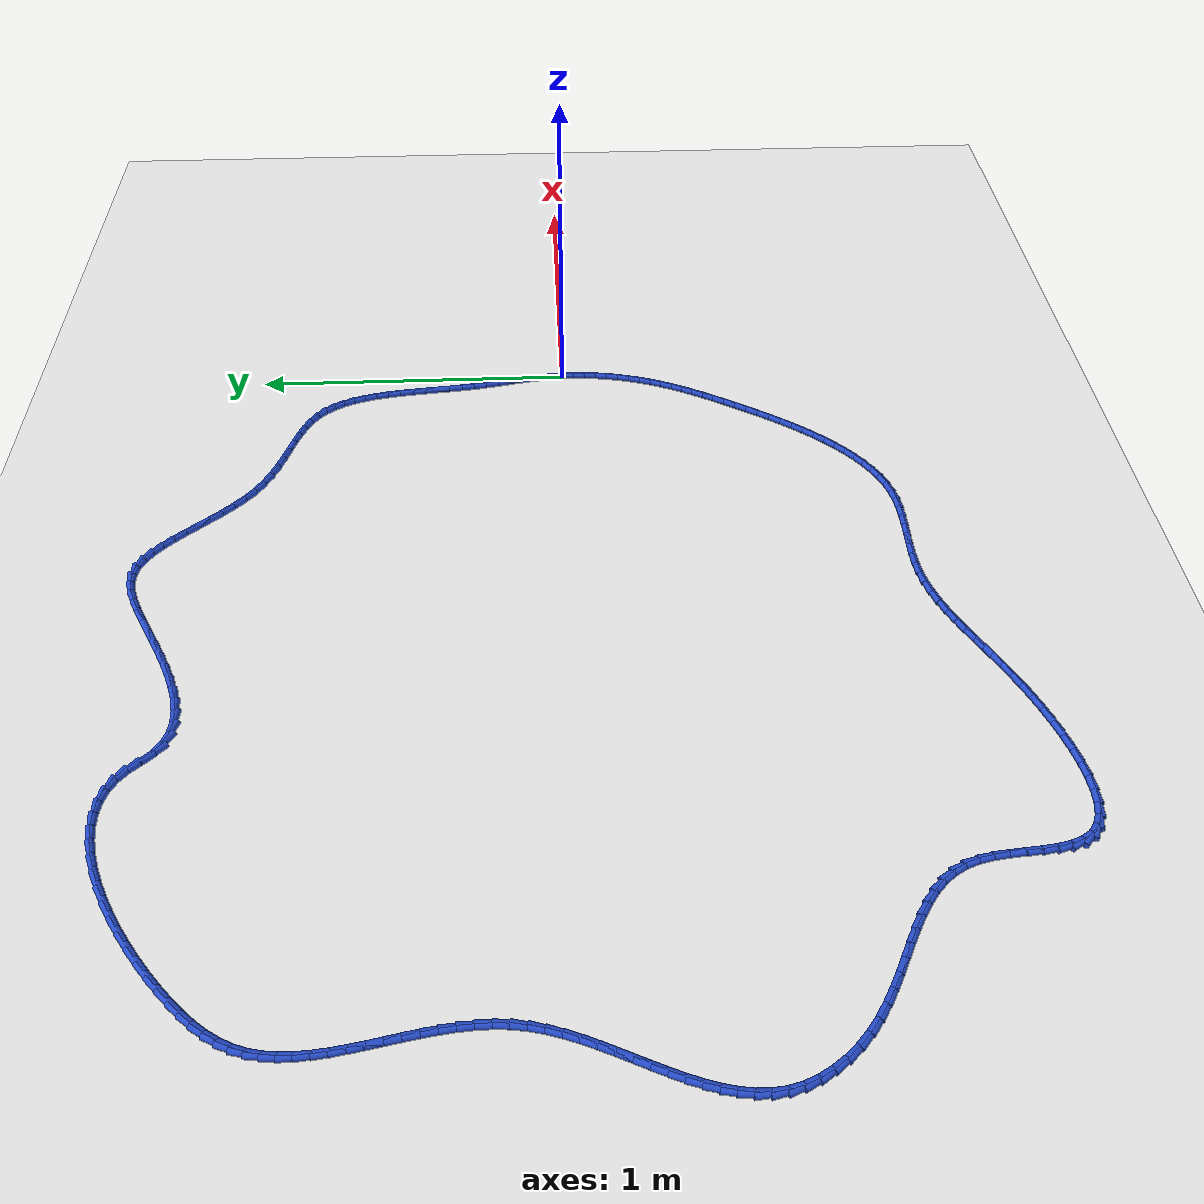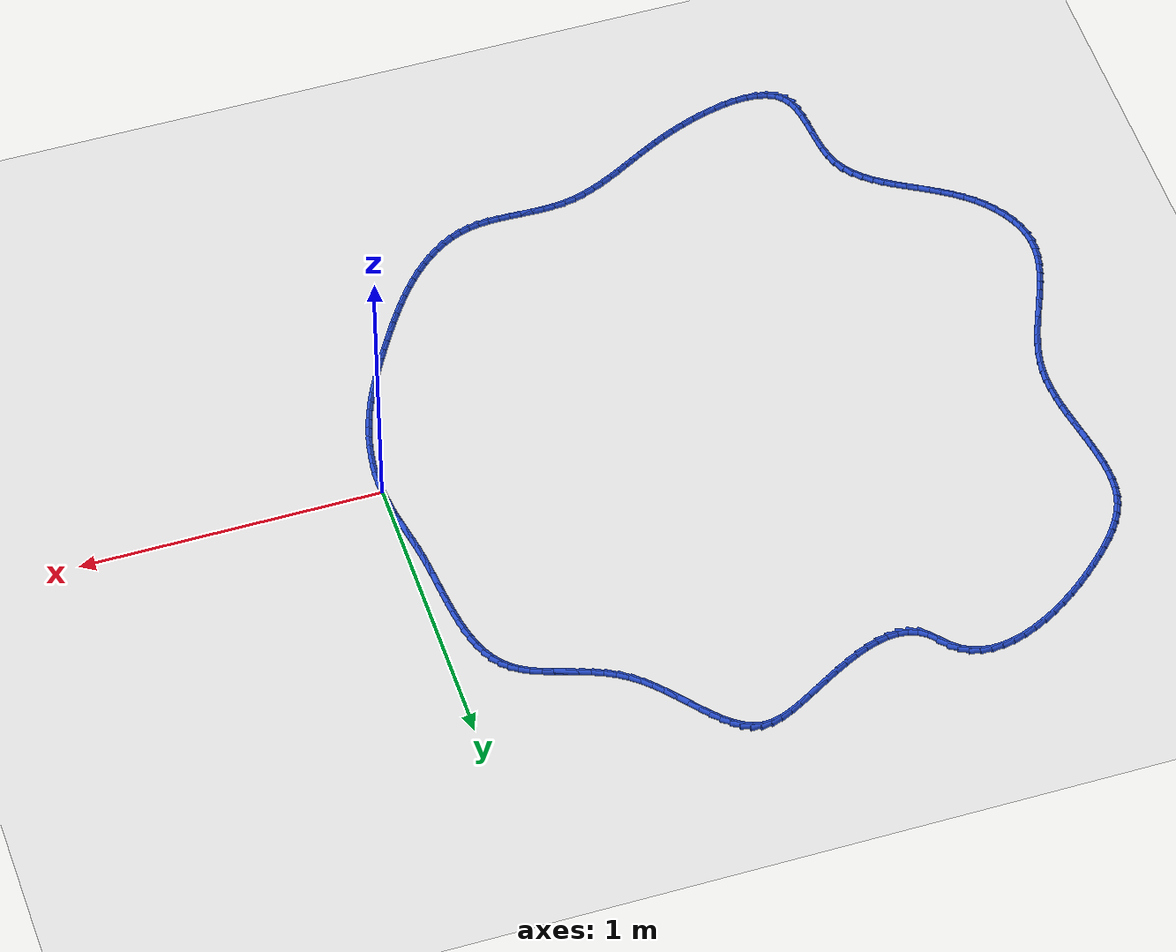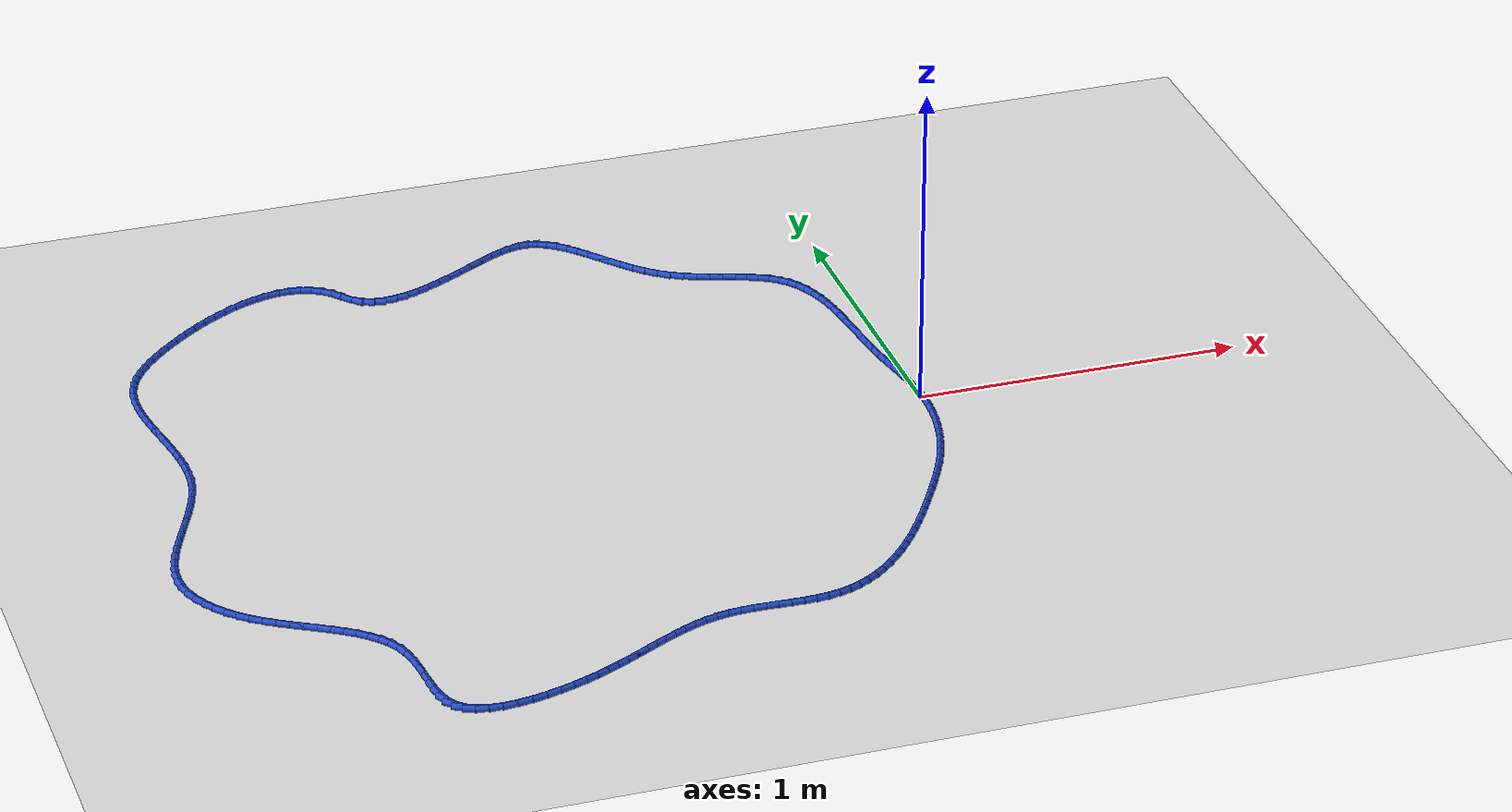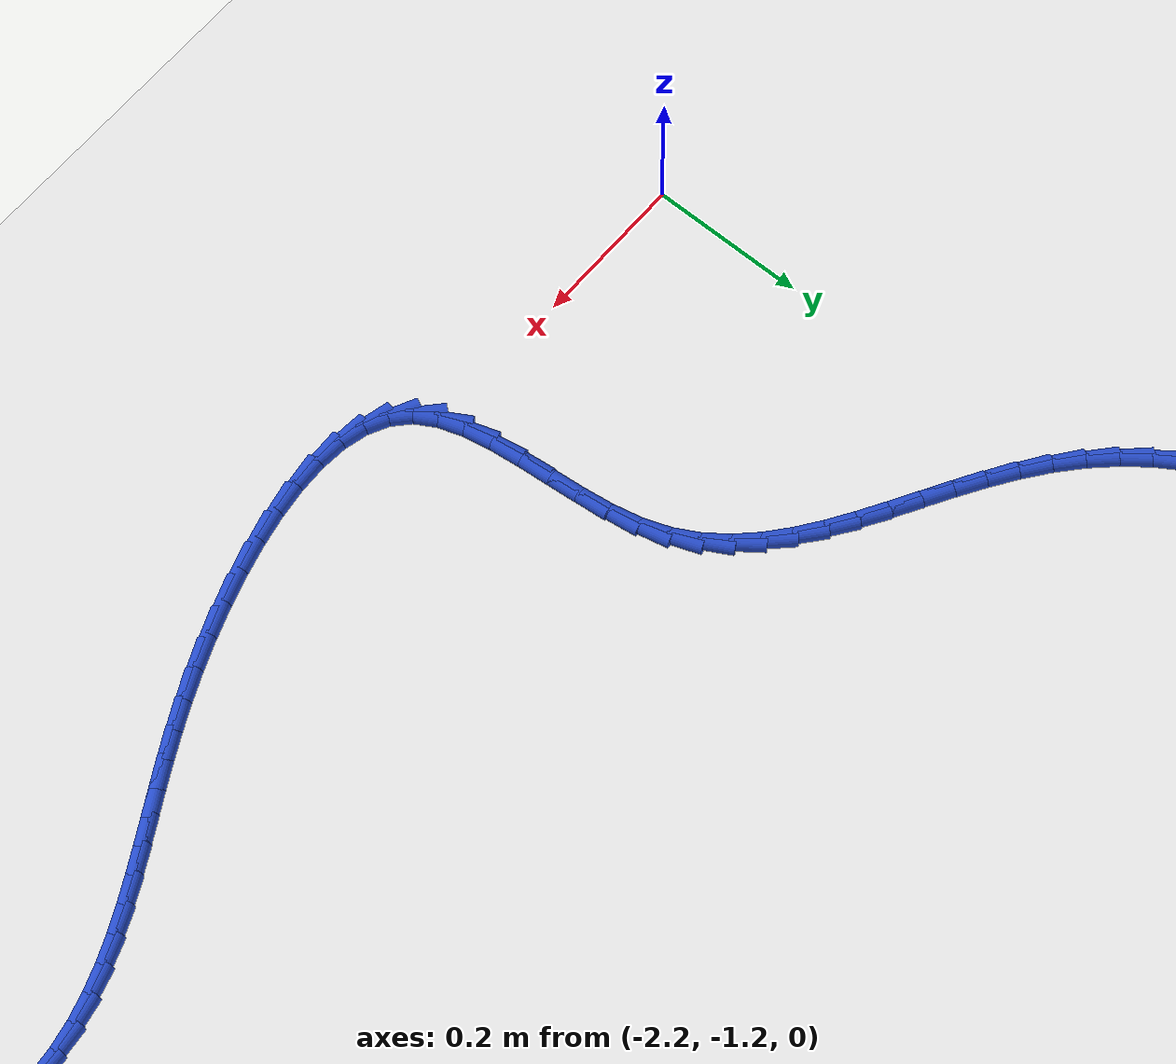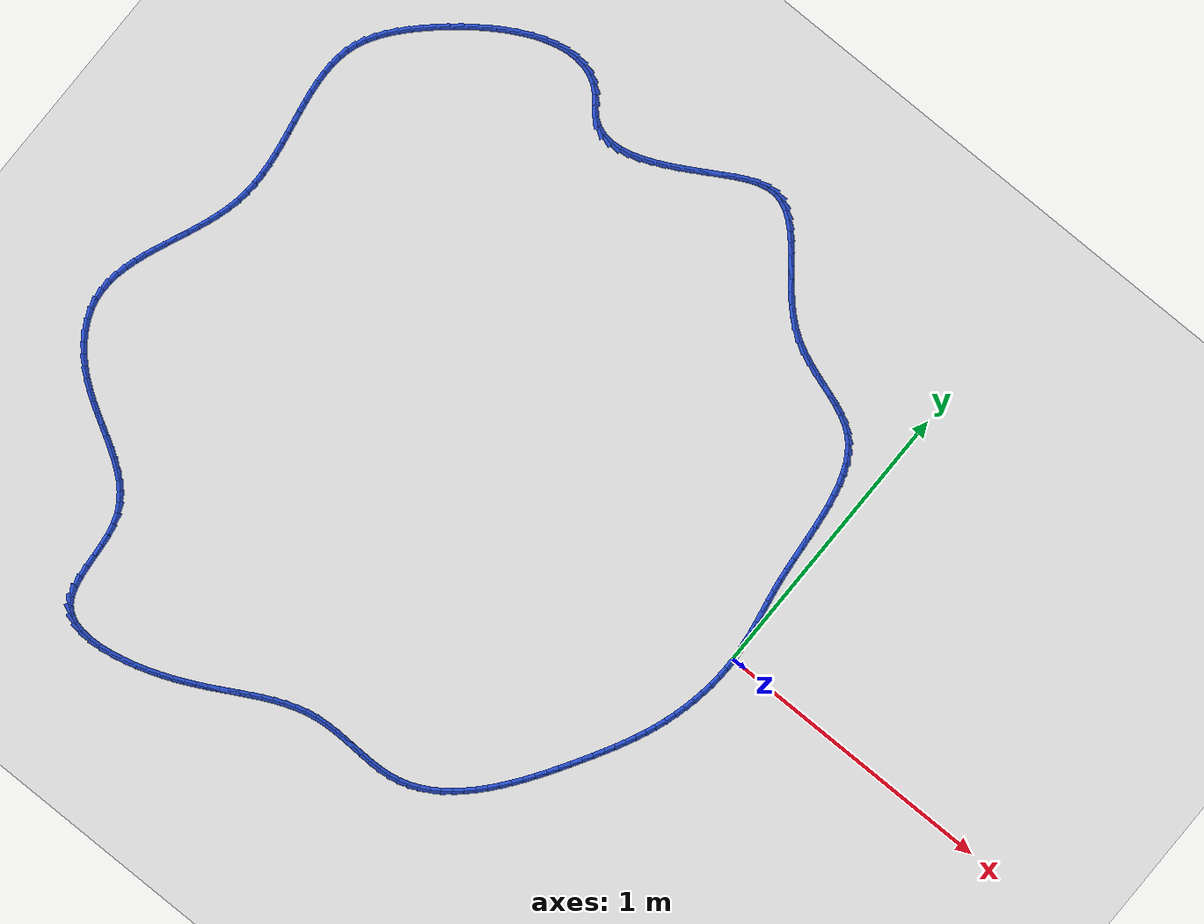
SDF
<sdf version="1.6">
 <world name="default">
  <light name="sun" type="directional">
   <pose>0 0 10 0 -0 0</pose>
   <diffuse>0.8 0.8 0.8 1</diffuse>
   <specular>0.2 0.2 0.2 1</specular>
   <attenuation>
    <range>1000</range>
    <constant>0.9</constant>
    <linear>0.01</linear>
    <quadratic>0.001</quadratic>
   </attenuation>
   <direction>-0.5 0.1 -0.9</direction>
  </light>
  <model name="ground_plane">
   <static>1</static>
   <link name="link">
    <collision name="collision">
     <geometry><plane><normal>0 0 1</normal><size>100 100</size></plane></geometry>
     <surface><friction><ode><mu>100</mu><mu2>50</mu2></ode></friction></surface>
    </collision>
    <visual name="visual">
     <cast_shadows>0</cast_shadows>
     <geometry><plane><normal>0 0 1</normal><size>100 100</size></plane></geometry>
     <material>
      <script><uri>file://media/materials/scripts/gazebo.material</uri><name>Gazebo/WhiteGlow</name></script>
     </material>
    </visual>
   </link>
  </model>
  <gravity>0 0 -9.8</gravity>
  <magnetic_field>6e-06 2.3e-05 -4.2e-05</magnetic_field>
  <atmosphere type="adiabatic"/>
  <physics name="default_physics" default="0" type="ode">
   <max_step_size>0.001</max_step_size>
   <real_time_factor>1</real_time_factor>
   <real_time_update_rate>1000</real_time_update_rate>
  </physics>
  <scene><ambient>0.4 0.4 0.4 1</ambient><background>0.7 0.7 0.7 1</background><shadows>1</shadows></scene>
  <spherical_coordinates>
   <surface_model>EARTH_WGS84</surface_model>
   <latitude_deg>0</latitude_deg>
   <longitude_deg>0</longitude_deg>
   <elevation>0</elevation>
   <heading_deg>0</heading_deg>
  </spherical_coordinates>
  <model name="line">
   <link name="link_0">
    <pose>-1.5612511283791264e-17 3.469446951953614e-17 0.01 0 1.57 -1.5016999985194608</pose>
    <collision name="collision">
     <geometry><cylinder><radius>0.01</radius><length>0.08</length></cylinder></geometry>
    </collision>
    <visual name="visual">
     <material>
      <script><name>Gazebo/Blue</name><uri>file://media/materials/scripts/gazebo.material</uri></script>
     </material>
     <geometry><cylinder><radius>0.01</radius><length>0.08</length></cylinder></geometry>
    </visual>
   </link>
   <link name="link_1">
    <pose>-0.002526843220174752 0.03651164537867711 0.01 0 1.57 -1.4563035895130598</pose>
    <collision name="collision">
     <geometry><cylinder><radius>0.01</radius><length>0.08</length></cylinder></geometry>
    </collision>
    <visual name="visual">
     <material>
      <script><name>Gazebo/Blue</name><uri>file://media/materials/scripts/gazebo.material</uri></script>
     </material>
     <geometry><cylinder><radius>0.01</radius><length>0.08</length></cylinder></geometry>
    </visual>
   </link>
   <link name="link_2">
    <pose>-0.006690340870274246 0.07271734109803088 0.01 0 1.57 -1.4219347301383096</pose>
    <collision name="collision">
     <geometry><cylinder><radius>0.01</radius><length>0.08</length></cylinder></geometry>
    </collision>
    <visual name="visual">
     <material>
      <script><name>Gazebo/Blue</name><uri>file://media/materials/scripts/gazebo.material</uri></script>
     </material>
     <geometry><cylinder><radius>0.01</radius><length>0.08</length></cylinder></geometry>
    </visual>
   </link>
   <link name="link_3">
    <pose>-0.012106982899735195 0.10883526804570957 0.01 0 1.57 -1.3990817266237026</pose>
    <collision name="collision">
     <geometry><cylinder><radius>0.01</radius><length>0.08</length></cylinder></geometry>
    </collision>
    <visual name="visual">
     <material>
      <script><name>Gazebo/Blue</name><uri>file://media/materials/scripts/gazebo.material</uri></script>
     </material>
     <geometry><cylinder><radius>0.01</radius><length>0.08</length></cylinder></geometry>
    </visual>
   </link>
   <link name="link_4">
    <pose>-0.018393259257994274 0.14508360710936144 0.01 0 1.57 -1.3878125602143352</pose>
    <collision name="collision">
     <geometry><cylinder><radius>0.01</radius><length>0.08</length></cylinder></geometry>
    </collision>
    <visual name="visual">
     <material>
      <script><name>Gazebo/Blue</name><uri>file://media/materials/scripts/gazebo.material</uri></script>
     </material>
     <geometry><cylinder><radius>0.01</radius><length>0.08</length></cylinder></geometry>
    </visual>
   </link>
   <link name="link_5">
    <pose>-0.025165659894488185 0.18168053917663468 0.01 0 1.57 -1.387871604505753</pose>
    <collision name="collision">
     <geometry><cylinder><radius>0.01</radius><length>0.08</length></cylinder></geometry>
    </collision>
    <visual name="visual">
     <material>
      <script><name>Gazebo/Blue</name><uri>file://media/materials/scripts/gazebo.material</uri></script>
     </material>
     <geometry><cylinder><radius>0.01</radius><length>0.08</length></cylinder></geometry>
    </visual>
   </link>
   <link name="link_6">
    <pose>-0.03204067475865362 0.21884424513517758 0.01 0 1.57 -1.3987499802710017</pose>
    <collision name="collision">
     <geometry><cylinder><radius>0.01</radius><length>0.08</length></cylinder></geometry>
    </collision>
    <visual name="visual">
     <material>
      <script><name>Gazebo/Blue</name><uri>file://media/materials/scripts/gazebo.material</uri></script>
     </material>
     <geometry><cylinder><radius>0.01</radius><length>0.08</length></cylinder></geometry>
    </visual>
   </link>
   <link name="link_7">
    <pose>-0.03863479379992725 0.25679290587263837 0.01 0 1.57 -1.4197240757113372</pose>
    <collision name="collision">
     <geometry><cylinder><radius>0.01</radius><length>0.08</length></cylinder></geometry>
    </collision>
    <visual name="visual">
     <material>
      <script><name>Gazebo/Blue</name><uri>file://media/materials/scripts/gazebo.material</uri></script>
     </material>
     <geometry><cylinder><radius>0.01</radius><length>0.08</length></cylinder></geometry>
    </visual>
   </link>
   <link name="link_8">
    <pose>-0.04456450887442466 0.29574470076258474 0.01 0 1.57 -1.4463464657182925</pose>
    <collision name="collision">
     <geometry><cylinder><radius>0.01</radius><length>0.08</length></cylinder></geometry>
    </collision>
    <visual name="visual">
     <material>
      <script><name>Gazebo/Blue</name><uri>file://media/materials/scripts/gazebo.material</uri></script>
     </material>
     <geometry><cylinder><radius>0.01</radius><length>0.08</length></cylinder></geometry>
    </visual>
   </link>
   <link name="link_9">
    <pose>-0.04957703255089371 0.33581400476692475 0.01 0 1.57 -1.4654200131653208</pose>
    <collision name="collision">
     <geometry><cylinder><radius>0.01</radius><length>0.08</length></cylinder></geometry>
    </collision>
    <visual name="visual">
     <material>
      <script><name>Gazebo/Blue</name><uri>file://media/materials/scripts/gazebo.material</uri></script>
     </material>
     <geometry><cylinder><radius>0.01</radius><length>0.08</length></cylinder></geometry>
    </visual>
   </link>
   <link name="link_10">
    <pose>-0.05390464015703279 0.3767300078734568 0.01 0 1.57 -1.4747831557251565</pose>
    <collision name="collision">
     <geometry><cylinder><radius>0.01</radius><length>0.08</length></cylinder></geometry>
    </collision>
    <visual name="visual">
     <material>
      <script><name>Gazebo/Blue</name><uri>file://media/materials/scripts/gazebo.material</uri></script>
     </material>
     <geometry><cylinder><radius>0.01</radius><length>0.08</length></cylinder></geometry>
    </visual>
   </link>
   <link name="link_11">
    <pose>-0.0578920923860259 0.4181325762210687 0.01 0 1.57 -1.4749637945693326</pose>
    <collision name="collision">
     <geometry><cylinder><radius>0.01</radius><length>0.08</length></cylinder></geometry>
    </collision>
    <visual name="visual">
     <material>
      <script><name>Gazebo/Blue</name><uri>file://media/materials/scripts/gazebo.material</uri></script>
     </material>
     <geometry><cylinder><radius>0.01</radius><length>0.08</length></cylinder></geometry>
    </visual>
   </link>
   <link name="link_12">
    <pose>-0.061884149931057175 0.459661575948649 0.01 0 1.57 -1.4660499159993419</pose>
    <collision name="collision">
     <geometry><cylinder><radius>0.01</radius><length>0.08</length></cylinder></geometry>
    </collision>
    <visual name="visual">
     <material>
      <script><name>Gazebo/Blue</name><uri>file://media/materials/scripts/gazebo.material</uri></script>
     </material>
     <geometry><cylinder><radius>0.01</radius><length>0.08</length></cylinder></geometry>
    </visual>
   </link>
   <link name="link_13">
    <pose>-0.06622557348531065 0.5009568731950858 0.01 0 1.57 -1.4477026723787587</pose>
    <collision name="collision">
     <geometry><cylinder><radius>0.01</radius><length>0.08</length></cylinder></geometry>
    </collision>
    <visual name="visual">
     <material>
      <script><name>Gazebo/Blue</name><uri>file://media/materials/scripts/gazebo.material</uri></script>
     </material>
     <geometry><cylinder><radius>0.01</radius><length>0.08</length></cylinder></geometry>
    </visual>
   </link>
   <link name="link_14">
    <pose>-0.07126112374197045 0.5416583340992676 0.01 0 1.57 -1.4191440212636472</pose>
    <collision name="collision">
     <geometry><cylinder><radius>0.01</radius><length>0.08</length></cylinder></geometry>
    </collision>
    <visual name="visual">
     <material>
      <script><name>Gazebo/Blue</name><uri>file://media/materials/scripts/gazebo.material</uri></script>
     </material>
     <geometry><cylinder><radius>0.01</radius><length>0.08</length></cylinder></geometry>
    </visual>
   </link>
   <link name="link_15">
    <pose>-0.07733556139422057 0.581405824800082 0.01 0 1.57 -1.379126228854976</pose>
    <collision name="collision">
     <geometry><cylinder><radius>0.01</radius><length>0.08</length></cylinder></geometry>
    </collision>
    <visual name="visual">
     <material>
      <script><name>Gazebo/Blue</name><uri>file://media/materials/scripts/gazebo.material</uri></script>
     </material>
     <geometry><cylinder><radius>0.01</radius><length>0.08</length></cylinder></geometry>
    </visual>
   </link>
   <link name="link_16">
    <pose>-0.08479364713524515 0.6198392114364177 0.01 0 1.57 -1.325901970148176</pose>
    <collision name="collision">
     <geometry><cylinder><radius>0.01</radius><length>0.08</length></cylinder></geometry>
    </collision>
    <visual name="visual">
     <material>
      <script><name>Gazebo/Blue</name><uri>file://media/materials/scripts/gazebo.material</uri></script>
     </material>
     <geometry><cylinder><radius>0.01</radius><length>0.08</length></cylinder></geometry>
    </visual>
   </link>
   <link name="link_17">
    <pose>-0.09398014165822824 0.6565983601471629 0.01 0 1.57 -1.2572388854309717</pose>
    <collision name="collision">
     <geometry><cylinder><radius>0.01</radius><length>0.08</length></cylinder></geometry>
    </collision>
    <visual name="visual">
     <material>
      <script><name>Gazebo/Blue</name><uri>file://media/materials/scripts/gazebo.material</uri></script>
     </material>
     <geometry><cylinder><radius>0.01</radius><length>0.08</length></cylinder></geometry>
    </visual>
   </link>
   <link name="link_18">
    <pose>-0.10523980565635388 0.6913231370712055 0.01 0 1.57 -1.170571345920834</pose>
    <collision name="collision">
     <geometry><cylinder><radius>0.01</radius><length>0.08</length></cylinder></geometry>
    </collision>
    <visual name="visual">
     <material>
      <script><name>Gazebo/Blue</name><uri>file://media/materials/scripts/gazebo.material</uri></script>
     </material>
     <geometry><cylinder><radius>0.01</radius><length>0.08</length></cylinder></geometry>
    </visual>
   </link>
   <link name="link_19">
    <pose>-0.11891739982280622 0.7236534083474341 0.01 0 1.57 -1.0634555412669138</pose>
    <collision name="collision">
     <geometry><cylinder><radius>0.01</radius><length>0.08</length></cylinder></geometry>
    </collision>
    <visual name="visual">
     <material>
      <script><name>Gazebo/Blue</name><uri>file://media/materials/scripts/gazebo.material</uri></script>
     </material>
     <geometry><cylinder><radius>0.01</radius><length>0.08</length></cylinder></geometry>
    </visual>
   </link>
   <link name="link_20">
    <pose>-0.13535768485076927 0.7532290401147367 0.01 0 1.57 -0.9345396239350764</pose>
    <collision name="collision">
     <geometry><cylinder><radius>0.01</radius><length>0.08</length></cylinder></geometry>
    </collision>
    <visual name="visual">
     <material>
      <script><name>Gazebo/Blue</name><uri>file://media/materials/scripts/gazebo.material</uri></script>
     </material>
     <geometry><cylinder><radius>0.01</radius><length>0.08</length></cylinder></geometry>
    </visual>
   </link>
   <link name="link_21">
    <pose>-0.15490542143342712 0.7796898985120015 0.01 0 1.57 -0.7850937730519277</pose>
    <collision name="collision">
     <geometry><cylinder><radius>0.01</radius><length>0.08</length></cylinder></geometry>
    </collision>
    <visual name="visual">
     <material>
      <script><name>Gazebo/Blue</name><uri>file://media/materials/scripts/gazebo.material</uri></script>
     </material>
     <geometry><cylinder><radius>0.01</radius><length>0.08</length></cylinder></geometry>
    </visual>
   </link>
   <link name="link_22">
    <pose>-0.17790537026396383 0.8026758496781169 0.01 0 1.57 -0.6264064705719183</pose>
    <collision name="collision">
     <geometry><cylinder><radius>0.01</radius><length>0.08</length></cylinder></geometry>
    </collision>
    <visual name="visual">
     <material>
      <script><name>Gazebo/Blue</name><uri>file://media/materials/scripts/gazebo.material</uri></script>
     </material>
     <geometry><cylinder><radius>0.01</radius><length>0.08</length></cylinder></geometry>
    </visual>
   </link>
   <link name="link_23">
    <pose>-0.2045810512284153 0.8219790448971042 0.01 0 1.57 -0.4961131739949698</pose>
    <collision name="collision">
     <geometry><cylinder><radius>0.01</radius><length>0.08</length></cylinder></geometry>
    </collision>
    <visual name="visual">
     <material>
      <script><name>Gazebo/Blue</name><uri>file://media/materials/scripts/gazebo.material</uri></script>
     </material>
     <geometry><cylinder><radius>0.01</radius><length>0.08</length></cylinder></geometry>
    </visual>
   </link>
   <link name="link_24">
    <pose>-0.2345236037591797 0.8381859402042201 0.01 0 1.57 -0.4045256632904601</pose>
    <collision name="collision">
     <geometry><cylinder><radius>0.01</radius><length>0.08</length></cylinder></geometry>
    </collision>
    <visual name="visual">
     <material>
      <script><name>Gazebo/Blue</name><uri>file://media/materials/scripts/gazebo.material</uri></script>
     </material>
     <geometry><cylinder><radius>0.01</radius><length>0.08</length></cylinder></geometry>
    </visual>
   </link>
   <link name="link_25">
    <pose>-0.26711865620953484 0.8521411248923817 0.01 0 1.57 -0.34760650934976645</pose>
    <collision name="collision">
     <geometry><cylinder><radius>0.01</radius><length>0.08</length></cylinder></geometry>
    </collision>
    <visual name="visual">
     <material>
      <script><name>Gazebo/Blue</name><uri>file://media/materials/scripts/gazebo.material</uri></script>
     </material>
     <geometry><cylinder><radius>0.01</radius><length>0.08</length></cylinder></geometry>
    </visual>
   </link>
   <link name="link_26">
    <pose>-0.30175172769079317 0.8646893254684409 0.01 0 1.57 -0.32092844916377644</pose>
    <collision name="collision">
     <geometry><cylinder><radius>0.01</radius><length>0.08</length></cylinder></geometry>
    </collision>
    <visual name="visual">
     <material>
      <script><name>Gazebo/Blue</name><uri>file://media/materials/scripts/gazebo.material</uri></script>
     </material>
     <geometry><cylinder><radius>0.01</radius><length>0.08</length></cylinder></geometry>
    </visual>
   </link>
   <link name="link_27">
    <pose>-0.3378083373142678 0.8766752684392513 0.01 0 1.57 -0.32125870519632155</pose>
    <collision name="collision">
     <geometry><cylinder><radius>0.01</radius><length>0.08</length></cylinder></geometry>
    </collision>
    <visual name="visual">
     <material>
      <script><name>Gazebo/Blue</name><uri>file://media/materials/scripts/gazebo.material</uri></script>
     </material>
     <geometry><cylinder><radius>0.01</radius><length>0.08</length></cylinder></geometry>
    </visual>
   </link>
   <link name="link_28">
    <pose>-0.37467400419127145 0.8889436803116658 0.01 0 1.57 -0.3468429792717593</pose>
    <collision name="collision">
     <geometry><cylinder><radius>0.01</radius><length>0.08</length></cylinder></geometry>
    </collision>
    <visual name="visual">
     <material>
      <script><name>Gazebo/Blue</name><uri>file://media/materials/scripts/gazebo.material</uri></script>
     </material>
     <geometry><cylinder><radius>0.01</radius><length>0.08</length></cylinder></geometry>
    </visual>
   </link>
   <link name="link_29">
    <pose>-0.4117342474331166 0.9023392875925369 0.01 0 1.57 -0.3971311076099659</pose>
    <collision name="collision">
     <geometry><cylinder><radius>0.01</radius><length>0.08</length></cylinder></geometry>
    </collision>
    <visual name="visual">
     <material>
      <script><name>Gazebo/Blue</name><uri>file://media/materials/scripts/gazebo.material</uri></script>
     </material>
     <geometry><cylinder><radius>0.01</radius><length>0.08</length></cylinder></geometry>
    </visual>
   </link>
   <link name="link_30">
    <pose>-0.44837458615111664 0.917706816788718 0.01 0 1.57 -0.472175761600495</pose>
    <collision name="collision">
     <geometry><cylinder><radius>0.01</radius><length>0.08</length></cylinder></geometry>
    </collision>
    <visual name="visual">
     <material>
      <script><name>Gazebo/Blue</name><uri>file://media/materials/scripts/gazebo.material</uri></script>
     </material>
     <geometry><cylinder><radius>0.01</radius><length>0.08</length></cylinder></geometry>
    </visual>
   </link>
   <link name="link_31">
    <pose>-0.4839805394565837 0.9358909944070615 0.01 0 1.57 -0.5716167457707252</pose>
    <collision name="collision">
     <geometry><cylinder><radius>0.01</radius><length>0.08</length></cylinder></geometry>
    </collision>
    <visual name="visual">
     <material>
      <script><name>Gazebo/Blue</name><uri>file://media/materials/scripts/gazebo.material</uri></script>
     </material>
     <geometry><cylinder><radius>0.01</radius><length>0.08</length></cylinder></geometry>
    </visual>
   </link>
   <link name="link_32">
    <pose>-0.5179386151304062 0.957734590785243 0.01 0 1.57 -0.680156577747959</pose>
    <collision name="collision">
     <geometry><cylinder><radius>0.01</radius><length>0.08</length></cylinder></geometry>
    </collision>
    <visual name="visual">
     <material>
      <script><name>Gazebo/Blue</name><uri>file://media/materials/scripts/gazebo.material</uri></script>
     </material>
     <geometry><cylinder><radius>0.01</radius><length>0.08</length></cylinder></geometry>
    </visual>
   </link>
   <link name="link_33">
    <pose>-0.5498884769271363 0.9835794850374405 0.01 0 1.57 -0.7660693091415565</pose>
    <collision name="collision">
     <geometry><cylinder><radius>0.01</radius><length>0.08</length></cylinder></geometry>
    </collision>
    <visual name="visual">
     <material>
      <script><name>Gazebo/Blue</name><uri>file://media/materials/scripts/gazebo.material</uri></script>
     </material>
     <geometry><cylinder><radius>0.01</radius><length>0.08</length></cylinder></geometry>
    </visual>
   </link>
   <link name="link_34">
    <pose>-0.5800576699563843 1.0126043816272745 0.01 0 1.57 -0.8274237586824399</pose>
    <collision name="collision">
     <geometry><cylinder><radius>0.01</radius><length>0.08</length></cylinder></geometry>
    </collision>
    <visual name="visual">
     <material>
      <script><name>Gazebo/Blue</name><uri>file://media/materials/scripts/gazebo.material</uri></script>
     </material>
     <geometry><cylinder><radius>0.01</radius><length>0.08</length></cylinder></geometry>
    </visual>
   </link>
   <link name="link_35">
    <pose>-0.6087569841782909 1.043823277804751 0.01 0 1.57 -0.8667076220452137</pose>
    <collision name="collision">
     <geometry><cylinder><radius>0.01</radius><length>0.08</length></cylinder></geometry>
    </collision>
    <visual name="visual">
     <material>
      <script><name>Gazebo/Blue</name><uri>file://media/materials/scripts/gazebo.material</uri></script>
     </material>
     <geometry><cylinder><radius>0.01</radius><length>0.08</length></cylinder></geometry>
    </visual>
   </link>
   <link name="link_36">
    <pose>-0.6362972095529965 1.076250170819877 0.01 0 1.57 -0.8854485407357142</pose>
    <collision name="collision">
     <geometry><cylinder><radius>0.01</radius><length>0.08</length></cylinder></geometry>
    </collision>
    <visual name="visual">
     <material>
      <script><name>Gazebo/Blue</name><uri>file://media/materials/scripts/gazebo.material</uri></script>
     </material>
     <geometry><cylinder><radius>0.01</radius><length>0.08</length></cylinder></geometry>
    </visual>
   </link>
   <link name="link_37">
    <pose>-0.6629891360406418 1.1088990579226592 0.01 0 1.57 -0.883813348115418</pose>
    <collision name="collision">
     <geometry><cylinder><radius>0.01</radius><length>0.08</length></cylinder></geometry>
    </collision>
    <visual name="visual">
     <material>
      <script><name>Gazebo/Blue</name><uri>file://media/materials/scripts/gazebo.material</uri></script>
     </material>
     <geometry><cylinder><radius>0.01</radius><length>0.08</length></cylinder></geometry>
    </visual>
   </link>
   <link name="link_38">
    <pose>-0.6891435536013673 1.140783936363104 0.01 0 1.57 -0.8603019290900006</pose>
    <collision name="collision">
     <geometry><cylinder><radius>0.01</radius><length>0.08</length></cylinder></geometry>
    </collision>
    <visual name="visual">
     <material>
      <script><name>Gazebo/Blue</name><uri>file://media/materials/scripts/gazebo.material</uri></script>
     </material>
     <geometry><cylinder><radius>0.01</radius><length>0.08</length></cylinder></geometry>
    </visual>
   </link>
   <link name="link_39">
    <pose>-0.7150712521953132 1.170918803391218 0.01 0 1.57 -0.8113625034754526</pose>
    <collision name="collision">
     <geometry><cylinder><radius>0.01</radius><length>0.08</length></cylinder></geometry>
    </collision>
    <visual name="visual">
     <material>
      <script><name>Gazebo/Blue</name><uri>file://media/materials/scripts/gazebo.material</uri></script>
     </material>
     <geometry><cylinder><radius>0.01</radius><length>0.08</length></cylinder></geometry>
    </visual>
   </link>
   <link name="link_40">
    <pose>-0.7410830217826205 1.1983176562570081 0.01 0 1.57 -0.730947136426376</pose>
    <collision name="collision">
     <geometry><cylinder><radius>0.01</radius><length>0.08</length></cylinder></geometry>
    </collision>
    <visual name="visual">
     <material>
      <script><name>Gazebo/Blue</name><uri>file://media/materials/scripts/gazebo.material</uri></script>
     </material>
     <geometry><cylinder><radius>0.01</radius><length>0.08</length></cylinder></geometry>
    </visual>
   </link>
   <link name="link_41">
    <pose>-0.7674896523234294 1.2219944922104806 0.01 0 1.57 -0.6104838099672966</pose>
    <collision name="collision">
     <geometry><cylinder><radius>0.01</radius><length>0.08</length></cylinder></geometry>
    </collision>
    <visual name="visual">
     <material>
      <script><name>Gazebo/Blue</name><uri>file://media/materials/scripts/gazebo.material</uri></script>
     </material>
     <geometry><cylinder><radius>0.01</radius><length>0.08</length></cylinder></geometry>
    </visual>
   </link>
   <link name="link_42">
    <pose>-0.7946019337778807 1.2409633085016427 0.01 0 1.57 -0.4409406864053051</pose>
    <collision name="collision">
     <geometry><cylinder><radius>0.01</radius><length>0.08</length></cylinder></geometry>
    </collision>
    <visual name="visual">
     <material>
      <script><name>Gazebo/Blue</name><uri>file://media/materials/scripts/gazebo.material</uri></script>
     </material>
     <geometry><cylinder><radius>0.01</radius><length>0.08</length></cylinder></geometry>
    </visual>
   </link>
   <link name="link_43">
    <pose>-0.822730656106115 1.2542381023805003 0.01 0 1.57 -0.22025364822686827</pose>
    <collision name="collision">
     <geometry><cylinder><radius>0.01</radius><length>0.08</length></cylinder></geometry>
    </collision>
    <visual name="visual">
     <material>
      <script><name>Gazebo/Blue</name><uri>file://media/materials/scripts/gazebo.material</uri></script>
     </material>
     <geometry><cylinder><radius>0.01</radius><length>0.08</length></cylinder></geometry>
    </visual>
   </link>
   <link name="link_44">
    <pose>-0.8521866092682724 1.2608328710970604 0.01 0 1.57 0.029113691015340858</pose>
    <collision name="collision">
     <geometry><cylinder><radius>0.01</radius><length>0.08</length></cylinder></geometry>
    </collision>
    <visual name="visual">
     <material>
      <script><name>Gazebo/Blue</name><uri>file://media/materials/scripts/gazebo.material</uri></script>
     </material>
     <geometry><cylinder><radius>0.01</radius><length>0.08</length></cylinder></geometry>
    </visual>
   </link>
   <link name="link_45">
    <pose>-0.8832509540408516 1.2599282177504756 0.01 0 1.57 0.23449654743403953</pose>
    <collision name="collision">
     <geometry><cylinder><radius>0.01</radius><length>0.08</length></cylinder></geometry>
    </collision>
    <visual name="visual">
     <material>
      <script><name>Gazebo/Blue</name><uri>file://media/materials/scripts/gazebo.material</uri></script>
     </material>
     <geometry><cylinder><radius>0.01</radius><length>0.08</length></cylinder></geometry>
    </visual>
   </link>
   <link name="link_46">
    <pose>-0.9159539164724706 1.2521157594564798 0.01 0 1.57 0.3734422384207128</pose>
    <collision name="collision">
     <geometry><cylinder><radius>0.01</radius><length>0.08</length></cylinder></geometry>
    </collision>
    <visual name="visual">
     <material>
      <script><name>Gazebo/Blue</name><uri>file://media/materials/scripts/gazebo.material</uri></script>
     </material>
     <geometry><cylinder><radius>0.01</radius><length>0.08</length></cylinder></geometry>
    </visual>
   </link>
   <link name="link_47">
    <pose>-0.9501994053949284 1.2386973990890677 0.01 0 1.57 0.4607626281065297</pose>
    <collision name="collision">
     <geometry><cylinder><radius>0.01</radius><length>0.08</length></cylinder></geometry>
    </collision>
    <visual name="visual">
     <material>
      <script><name>Gazebo/Blue</name><uri>file://media/materials/scripts/gazebo.material</uri></script>
     </material>
     <geometry><cylinder><radius>0.01</radius><length>0.08</length></cylinder></geometry>
    </visual>
   </link>
   <link name="link_48">
    <pose>-0.9858903688633059 1.2209804420005115 0.01 0 1.57 0.5097932044655282</pose>
    <collision name="collision">
     <geometry><cylinder><radius>0.01</radius><length>0.08</length></cylinder></geometry>
    </collision>
    <visual name="visual">
     <material>
      <script><name>Gazebo/Blue</name><uri>file://media/materials/scripts/gazebo.material</uri></script>
     </material>
     <geometry><cylinder><radius>0.01</radius><length>0.08</length></cylinder></geometry>
    </visual>
   </link>
   <link name="link_49">
    <pose>-1.0229297549326837 1.2002721935430825 0.01 0 1.57 0.5293302936370584</pose>
    <collision name="collision">
     <geometry><cylinder><radius>0.01</radius><length>0.08</length></cylinder></geometry>
    </collision>
    <visual name="visual">
     <material>
      <script><name>Gazebo/Blue</name><uri>file://media/materials/scripts/gazebo.material</uri></script>
     </material>
     <geometry><cylinder><radius>0.01</radius><length>0.08</length></cylinder></geometry>
    </visual>
   </link>
   <link name="link_50">
    <pose>-1.0612163946157378 1.1778738297555482 0.01 0 1.57 0.5291321675905174</pose>
    <collision name="collision">
     <geometry><cylinder><radius>0.01</radius><length>0.08</length></cylinder></geometry>
    </collision>
    <visual name="visual">
     <material>
      <script><name>Gazebo/Blue</name><uri>file://media/materials/scripts/gazebo.material</uri></script>
     </material>
     <geometry><cylinder><radius>0.01</radius><length>0.08</length></cylinder></geometry>
    </visual>
   </link>
   <link name="link_51">
    <pose>-1.1005183965138143 1.1548919115713616 0.01 0 1.57 0.5167140897157266</pose>
    <collision name="collision">
     <geometry><cylinder><radius>0.01</radius><length>0.08</length></cylinder></geometry>
    </collision>
    <visual name="visual">
     <material>
      <script><name>Gazebo/Blue</name><uri>file://media/materials/scripts/gazebo.material</uri></script>
     </material>
     <geometry><cylinder><radius>0.01</radius><length>0.08</length></cylinder></geometry>
    </visual>
   </link>
   <link name="link_52">
    <pose>-1.1404493071504342 1.1322028931293782 0.01 0 1.57 0.4921242826165503</pose>
    <collision name="collision">
     <geometry><cylinder><radius>0.01</radius><length>0.08</length></cylinder></geometry>
    </collision>
    <visual name="visual">
     <material>
      <script><name>Gazebo/Blue</name><uri>file://media/materials/scripts/gazebo.material</uri></script>
     </material>
     <geometry><cylinder><radius>0.01</radius><length>0.08</length></cylinder></geometry>
    </visual>
   </link>
   <link name="link_53">
    <pose>-1.1806137460902888 1.1106699384140308 0.01 0 1.57 0.4538494542034885</pose>
    <collision name="collision">
     <geometry><cylinder><radius>0.01</radius><length>0.08</length></cylinder></geometry>
    </collision>
    <visual name="visual">
     <material>
      <script><name>Gazebo/Blue</name><uri>file://media/materials/scripts/gazebo.material</uri></script>
     </material>
     <geometry><cylinder><radius>0.01</radius><length>0.08</length></cylinder></geometry>
    </visual>
   </link>
   <link name="link_54">
    <pose>-1.2206163328980695 1.0911562114097548 0.01 0 1.57 0.3990125655813832</pose>
    <collision name="collision">
     <geometry><cylinder><radius>0.01</radius><length>0.08</length></cylinder></geometry>
    </collision>
    <visual name="visual">
     <material>
      <script><name>Gazebo/Blue</name><uri>file://media/materials/scripts/gazebo.material</uri></script>
     </material>
     <geometry><cylinder><radius>0.01</radius><length>0.08</length></cylinder></geometry>
    </visual>
   </link>
   <link name="link_55">
    <pose>-1.260061687138467 1.074524876100984 0.01 0 1.57 0.3230328263287502</pose>
    <collision name="collision">
     <geometry><cylinder><radius>0.01</radius><length>0.08</length></cylinder></geometry>
    </collision>
    <visual name="visual">
     <material>
      <script><name>Gazebo/Blue</name><uri>file://media/materials/scripts/gazebo.material</uri></script>
     </material>
     <geometry><cylinder><radius>0.01</radius><length>0.08</length></cylinder></geometry>
    </visual>
   </link>
   <link name="link_56">
    <pose>-1.2985544283761727 1.061639096472152 0.01 0 1.57 0.21925050515555328</pose>
    <collision name="collision">
     <geometry><cylinder><radius>0.01</radius><length>0.08</length></cylinder></geometry>
    </collision>
    <visual name="visual">
     <material>
      <script><name>Gazebo/Blue</name><uri>file://media/materials/scripts/gazebo.material</uri></script>
     </material>
     <geometry><cylinder><radius>0.01</radius><length>0.08</length></cylinder></geometry>
    </visual>
   </link>
   <link name="link_57">
    <pose>-1.3356991761758779 1.053362036507694 0.01 0 1.57 0.07907397174544131</pose>
    <collision name="collision">
     <geometry><cylinder><radius>0.01</radius><length>0.08</length></cylinder></geometry>
    </collision>
    <visual name="visual">
     <material>
      <script><name>Gazebo/Blue</name><uri>file://media/materials/scripts/gazebo.material</uri></script>
     </material>
     <geometry><cylinder><radius>0.01</radius><length>0.08</length></cylinder></geometry>
    </visual>
   </link>
   <link name="link_58">
    <pose>-1.3711005501022735 1.0505568601920439 0.01 0 1.57 -0.10572556728788335</pose>
    <collision name="collision">
     <geometry><cylinder><radius>0.01</radius><length>0.08</length></cylinder></geometry>
    </collision>
    <visual name="visual">
     <material>
      <script><name>Gazebo/Blue</name><uri>file://media/materials/scripts/gazebo.material</uri></script>
     </material>
     <geometry><cylinder><radius>0.01</radius><length>0.08</length></cylinder></geometry>
    </visual>
   </link>
   <link name="link_59">
    <pose>-1.404363169720051 1.0540867315096354 0.01 0 1.57 -0.3358951157535757</pose>
    <collision name="collision">
     <geometry><cylinder><radius>0.01</radius><length>0.08</length></cylinder></geometry>
    </collision>
    <visual name="visual">
     <material>
      <script><name>Gazebo/Blue</name><uri>file://media/materials/scripts/gazebo.material</uri></script>
     </material>
     <geometry><cylinder><radius>0.01</radius><length>0.08</length></cylinder></geometry>
    </visual>
   </link>
   <link name="link_60">
    <pose>-1.4350916545939016 1.0648148144449028 0.01 0 1.57 -0.5943710312892465</pose>
    <collision name="collision">
     <geometry><cylinder><radius>0.01</radius><length>0.08</length></cylinder></geometry>
    </collision>
    <visual name="visual">
     <material>
      <script><name>Gazebo/Blue</name><uri>file://media/materials/scripts/gazebo.material</uri></script>
     </material>
     <geometry><cylinder><radius>0.01</radius><length>0.08</length></cylinder></geometry>
    </visual>
   </link>
   <link name="link_61">
    <pose>-1.4628906242885162 1.0836042729822803 0.01 0 1.57 -0.8263065147633406</pose>
    <collision name="collision">
     <geometry><cylinder><radius>0.01</radius><length>0.08</length></cylinder></geometry>
    </collision>
    <visual name="visual">
     <material>
      <script><name>Gazebo/Blue</name><uri>file://media/materials/scripts/gazebo.material</uri></script>
     </material>
     <geometry><cylinder><radius>0.01</radius><length>0.08</length></cylinder></geometry>
    </visual>
   </link>
   <link name="link_62">
    <pose>-1.4876874850941624 1.110517697109729 0.01 0 1.57 -0.8735001498892482</pose>
    <collision name="collision">
     <geometry><cylinder><radius>0.01</radius><length>0.08</length></cylinder></geometry>
    </collision>
    <visual name="visual">
     <material>
      <script><name>Gazebo/Blue</name><uri>file://media/materials/scripts/gazebo.material</uri></script>
     </material>
     <geometry><cylinder><radius>0.01</radius><length>0.08</length></cylinder></geometry>
    </visual>
   </link>
   <link name="link_63">
    <pose>-1.5119051842288271 1.1394282488878325 0.01 0 1.57 -0.7202565079342788</pose>
    <collision name="collision">
     <geometry><cylinder><radius>0.01</radius><length>0.08</length></cylinder></geometry>
    </collision>
    <visual name="visual">
     <material>
      <script><name>Gazebo/Blue</name><uri>file://media/materials/scripts/gazebo.material</uri></script>
     </material>
     <geometry><cylinder><radius>0.01</radius><length>0.08</length></cylinder></geometry>
    </visual>
   </link>
   <link name="link_64">
    <pose>-1.5385237035790633 1.1627865806515727 0.01 0 1.57 -0.5131491003804508</pose>
    <collision name="collision">
     <geometry><cylinder><radius>0.01</radius><length>0.08</length></cylinder></geometry>
    </collision>
    <visual name="visual">
     <material>
      <script><name>Gazebo/Blue</name><uri>file://media/materials/scripts/gazebo.material</uri></script>
     </material>
     <geometry><cylinder><radius>0.01</radius><length>0.08</length></cylinder></geometry>
    </visual>
   </link>
   <link name="link_65">
    <pose>-1.5679104527633096 1.1793460262359141 0.01 0 1.57 -0.3108375934351968</pose>
    <collision name="collision">
     <geometry><cylinder><radius>0.01</radius><length>0.08</length></cylinder></geometry>
    </collision>
    <visual name="visual">
     <material>
      <script><name>Gazebo/Blue</name><uri>file://media/materials/scripts/gazebo.material</uri></script>
     </material>
     <geometry><cylinder><radius>0.01</radius><length>0.08</length></cylinder></geometry>
    </visual>
   </link>
   <link name="link_66">
    <pose>-1.5997254298082269 1.1895666287103381 0.01 0 1.57 -0.1273721965579721</pose>
    <collision name="collision">
     <geometry><cylinder><radius>0.01</radius><length>0.08</length></cylinder></geometry>
    </collision>
    <visual name="visual">
     <material>
      <script><name>Gazebo/Blue</name><uri>file://media/materials/scripts/gazebo.material</uri></script>
     </material>
     <geometry><cylinder><radius>0.01</radius><length>0.08</length></cylinder></geometry>
    </visual>
   </link>
   <link name="link_67">
    <pose>-1.6336286214904598 1.1939084582862414 0.01 0 1.57 0.03019645772132437</pose>
    <collision name="collision">
     <geometry><cylinder><radius>0.01</radius><length>0.08</length></cylinder></geometry>
    </collision>
    <visual name="visual">
     <material>
      <script><name>Gazebo/Blue</name><uri>file://media/materials/scripts/gazebo.material</uri></script>
     </material>
     <geometry><cylinder><radius>0.01</radius><length>0.08</length></cylinder></geometry>
    </visual>
   </link>
   <link name="link_68">
    <pose>-1.6692800145866542 1.1928315851750193 0.01 0 1.57 0.16144215438989382</pose>
    <collision name="collision">
     <geometry><cylinder><radius>0.01</radius><length>0.08</length></cylinder></geometry>
    </collision>
    <visual name="visual">
     <material>
      <script><name>Gazebo/Blue</name><uri>file://media/materials/scripts/gazebo.material</uri></script>
     </material>
     <geometry><cylinder><radius>0.01</radius><length>0.08</length></cylinder></geometry>
    </visual>
   </link>
   <link name="link_69">
    <pose>-1.7063395958734566 1.1867960795880688 0.01 0 1.57 0.2695590276181311</pose>
    <collision name="collision">
     <geometry><cylinder><radius>0.01</radius><length>0.08</length></cylinder></geometry>
    </collision>
    <visual name="visual">
     <material>
      <script><name>Gazebo/Blue</name><uri>file://media/materials/scripts/gazebo.material</uri></script>
     </material>
     <geometry><cylinder><radius>0.01</radius><length>0.08</length></cylinder></geometry>
    </visual>
   </link>
   <link name="link_70">
    <pose>-1.7444673521275116 1.1762620117367861 0.01 0 1.57 0.3588065599918949</pose>
    <collision name="collision">
     <geometry><cylinder><radius>0.01</radius><length>0.08</length></cylinder></geometry>
    </collision>
    <visual name="visual">
     <material>
      <script><name>Gazebo/Blue</name><uri>file://media/materials/scripts/gazebo.material</uri></script>
     </material>
     <geometry><cylinder><radius>0.01</radius><length>0.08</length></cylinder></geometry>
    </visual>
   </link>
   <link name="link_71">
    <pose>-1.783323270125464 1.1616894518325669 0.01 0 1.57 0.43321278377351413</pose>
    <collision name="collision">
     <geometry><cylinder><radius>0.01</radius><length>0.08</length></cylinder></geometry>
    </collision>
    <visual name="visual">
     <material>
      <script><name>Gazebo/Blue</name><uri>file://media/materials/scripts/gazebo.material</uri></script>
     </material>
     <geometry><cylinder><radius>0.01</radius><length>0.08</length></cylinder></geometry>
    </visual>
   </link>
   <link name="link_72">
    <pose>-1.8225673366439603 1.1435384700868079 0.01 0 1.57 0.4961483633403605</pose>
    <collision name="collision">
     <geometry><cylinder><radius>0.01</radius><length>0.08</length></cylinder></geometry>
    </collision>
    <visual name="visual">
     <material>
      <script><name>Gazebo/Blue</name><uri>file://media/materials/scripts/gazebo.material</uri></script>
     </material>
     <geometry><cylinder><radius>0.01</radius><length>0.08</length></cylinder></geometry>
    </visual>
   </link>
   <link name="link_73">
    <pose>-1.8618595384596466 1.1222691367109043 0.01 0 1.57 0.5503039454989364</pose>
    <collision name="collision">
     <geometry><cylinder><radius>0.01</radius><length>0.08</length></cylinder></geometry>
    </collision>
    <visual name="visual">
     <material>
      <script><name>Gazebo/Blue</name><uri>file://media/materials/scripts/gazebo.material</uri></script>
     </material>
     <geometry><cylinder><radius>0.01</radius><length>0.08</length></cylinder></geometry>
    </visual>
   </link>
   <link name="link_74">
    <pose>-1.9008598623491666 1.0983415219162536 0.01 0 1.57 0.5978053632920111</pose>
    <collision name="collision">
     <geometry><cylinder><radius>0.01</radius><length>0.08</length></cylinder></geometry>
    </collision>
    <visual name="visual">
     <material>
      <script><name>Gazebo/Blue</name><uri>file://media/materials/scripts/gazebo.material</uri></script>
     </material>
     <geometry><cylinder><radius>0.01</radius><length>0.08</length></cylinder></geometry>
    </visual>
   </link>
   <link name="link_75">
    <pose>-1.939228295089167 1.0722156959142513 0.01 0 1.57 0.6403545227408854</pose>
    <collision name="collision">
     <geometry><cylinder><radius>0.01</radius><length>0.08</length></cylinder></geometry>
    </collision>
    <visual name="visual">
     <material>
      <script><name>Gazebo/Blue</name><uri>file://media/materials/scripts/gazebo.material</uri></script>
     </material>
     <geometry><cylinder><radius>0.01</radius><length>0.08</length></cylinder></geometry>
    </visual>
   </link>
   <link name="link_76">
    <pose>-1.9766248234562935 1.0443517289162931 0.01 0 1.57 0.6793597189799967</pose>
    <collision name="collision">
     <geometry><cylinder><radius>0.01</radius><length>0.08</length></cylinder></geometry>
    </collision>
    <visual name="visual">
     <material>
      <script><name>Gazebo/Blue</name><uri>file://media/materials/scripts/gazebo.material</uri></script>
     </material>
     <geometry><cylinder><radius>0.01</radius><length>0.08</length></cylinder></geometry>
    </visual>
   </link>
   <link name="link_77">
    <pose>-2.0127094342271907 1.0152096911337765 0.01 0 1.57 0.716050732968985</pose>
    <collision name="collision">
     <geometry><cylinder><radius>0.01</radius><length>0.08</length></cylinder></geometry>
    </collision>
    <visual name="visual">
     <material>
      <script><name>Gazebo/Blue</name><uri>file://media/materials/scripts/gazebo.material</uri></script>
     </material>
     <geometry><cylinder><radius>0.01</radius><length>0.08</length></cylinder></geometry>
    </visual>
   </link>
   <link name="link_78">
    <pose>-2.0471421141785044 0.9852496527780966 0.01 0 1.57 0.7515867866394877</pose>
    <collision name="collision">
     <geometry><cylinder><radius>0.01</radius><length>0.08</length></cylinder></geometry>
    </collision>
    <visual name="visual">
     <material>
      <script><name>Gazebo/Blue</name><uri>file://media/materials/scripts/gazebo.material</uri></script>
     </material>
     <geometry><cylinder><radius>0.01</radius><length>0.08</length></cylinder></geometry>
    </visual>
   </link>
   <link name="link_79">
    <pose>-2.0795828500868807 0.9549316840606497 0.01 0 1.57 0.7875512884475531</pose>
    <collision name="collision">
     <geometry><cylinder><radius>0.01</radius><length>0.08</length></cylinder></geometry>
    </collision>
    <visual name="visual">
     <material>
      <script><name>Gazebo/Blue</name><uri>file://media/materials/scripts/gazebo.material</uri></script>
     </material>
     <geometry><cylinder><radius>0.01</radius><length>0.08</length></cylinder></geometry>
    </visual>
   </link>
   <link name="link_80">
    <pose>-2.1096951903334493 0.9246893925437254 0.01 0 1.57 0.8306008485797518</pose>
    <collision name="collision">
     <geometry><cylinder><radius>0.01</radius><length>0.08</length></cylinder></geometry>
    </collision>
    <visual name="visual">
     <material>
      <script><name>Gazebo/Blue</name><uri>file://media/materials/scripts/gazebo.material</uri></script>
     </material>
     <geometry><cylinder><radius>0.01</radius><length>0.08</length></cylinder></geometry>
    </visual>
   </link>
   <link name="link_81">
    <pose>-2.137192439790786 0.8945866960670597 0.01 0 1.57 0.8861250071388266</pose>
    <collision name="collision">
     <geometry><cylinder><radius>0.01</radius><length>0.08</length></cylinder></geometry>
    </collision>
    <visual name="visual">
     <material>
      <script><name>Gazebo/Blue</name><uri>file://media/materials/scripts/gazebo.material</uri></script>
     </material>
     <geometry><cylinder><radius>0.01</radius><length>0.08</length></cylinder></geometry>
    </visual>
   </link>
   <link name="link_82">
    <pose>-2.1618244745609596 0.8644157889767922 0.01 0 1.57 0.9556697781211653</pose>
    <collision name="collision">
     <geometry><cylinder><radius>0.01</radius><length>0.08</length></cylinder></geometry>
    </collision>
    <visual name="visual">
     <material>
      <script><name>Gazebo/Blue</name><uri>file://media/materials/scripts/gazebo.material</uri></script>
     </material>
     <geometry><cylinder><radius>0.01</radius><length>0.08</length></cylinder></geometry>
    </visual>
   </link>
   <link name="link_83">
    <pose>-2.183342016690263 0.8339625802706198 0.01 0 1.57 1.0403184379333723</pose>
    <collision name="collision">
     <geometry><cylinder><radius>0.01</radius><length>0.08</length></cylinder></geometry>
    </collision>
    <visual name="visual">
     <material>
      <script><name>Gazebo/Blue</name><uri>file://media/materials/scripts/gazebo.material</uri></script>
     </material>
     <geometry><cylinder><radius>0.01</radius><length>0.08</length></cylinder></geometry>
    </visual>
   </link>
   <link name="link_84">
    <pose>-2.2014957882249906 0.8030129789462381 0.01 0 1.57 1.1402551556222162</pose>
    <collision name="collision">
     <geometry><cylinder><radius>0.01</radius><length>0.08</length></cylinder></geometry>
    </collision>
    <visual name="visual">
     <material>
      <script><name>Gazebo/Blue</name><uri>file://media/materials/scripts/gazebo.material</uri></script>
     </material>
     <geometry><cylinder><radius>0.01</radius><length>0.08</length></cylinder></geometry>
    </visual>
   </link>
   <link name="link_85">
    <pose>-2.216036511211436 0.7713528940013437 0.01 0 1.57 1.2538114602415407</pose>
    <collision name="collision">
     <geometry><cylinder><radius>0.01</radius><length>0.08</length></cylinder></geometry>
    </collision>
    <visual name="visual">
     <material>
      <script><name>Gazebo/Blue</name><uri>file://media/materials/scripts/gazebo.material</uri></script>
     </material>
     <geometry><cylinder><radius>0.01</radius><length>0.08</length></cylinder></geometry>
    </visual>
   </link>
   <link name="link_86">
    <pose>-2.2267244649467415 0.7387722864156653 0.01 0 1.57 1.3680088540732445</pose>
    <collision name="collision">
     <geometry><cylinder><radius>0.01</radius><length>0.08</length></cylinder></geometry>
    </collision>
    <visual name="visual">
     <material>
      <script><name>Gazebo/Blue</name><uri>file://media/materials/scripts/gazebo.material</uri></script>
     </material>
     <geometry><cylinder><radius>0.01</radius><length>0.08</length></cylinder></geometry>
    </visual>
   </link>
   <link name="link_87">
    <pose>-2.233629000136838 0.7051921539927031 0.01 0 1.57 1.4680030301778164</pose>
    <collision name="collision">
     <geometry><cylinder><radius>0.01</radius><length>0.08</length></cylinder></geometry>
    </collision>
    <visual name="visual">
     <material>
      <script><name>Gazebo/Blue</name><uri>file://media/materials/scripts/gazebo.material</uri></script>
     </material>
     <geometry><cylinder><radius>0.01</radius><length>0.08</length></cylinder></geometry>
    </visual>
   </link>
   <link name="link_88">
    <pose>-2.2371881548849935 0.6706898067154 0.01 0 1.57 1.5517424490350922</pose>
    <collision name="collision">
     <geometry><cylinder><radius>0.01</radius><length>0.08</length></cylinder></geometry>
    </collision>
    <visual name="visual">
     <material>
      <script><name>Gazebo/Blue</name><uri>file://media/materials/scripts/gazebo.material</uri></script>
     </material>
     <geometry><cylinder><radius>0.01</radius><length>0.08</length></cylinder></geometry>
    </visual>
   </link>
   <link name="link_89">
    <pose>-2.237861564137411 0.6353517109675242 0.01 0 1.57 -1.5222661975846603</pose>
    <collision name="collision">
     <geometry><cylinder><radius>0.01</radius><length>0.08</length></cylinder></geometry>
    </collision>
    <visual name="visual">
     <material>
      <script><name>Gazebo/Blue</name><uri>file://media/materials/scripts/gazebo.material</uri></script>
     </material>
     <geometry><cylinder><radius>0.01</radius><length>0.08</length></cylinder></geometry>
    </visual>
   </link>
   <link name="link_90">
    <pose>-2.236108862840295 0.5992643331328418 0.01 0 1.57 -1.469938153439032</pose>
    <collision name="collision">
     <geometry><cylinder><radius>0.01</radius><length>0.08</length></cylinder></geometry>
    </collision>
    <visual name="visual">
     <material>
      <script><name>Gazebo/Blue</name><uri>file://media/materials/scripts/gazebo.material</uri></script>
     </material>
     <geometry><cylinder><radius>0.01</radius><length>0.08</length></cylinder></geometry>
    </visual>
   </link>
   <link name="link_91">
    <pose>-2.2323896859398484 0.5625141395951193 0.01 0 1.57 -1.431692461719245</pose>
    <collision name="collision">
     <geometry><cylinder><radius>0.01</radius><length>0.08</length></cylinder></geometry>
    </collision>
    <visual name="visual">
     <material>
      <script><name>Gazebo/Blue</name><uri>file://media/materials/scripts/gazebo.material</uri></script>
     </material>
     <geometry><cylinder><radius>0.01</radius><length>0.08</length></cylinder></geometry>
    </visual>
   </link>
   <link name="link_92">
    <pose>-2.227163668382276 0.5251875967381237 0.01 0 1.57 -1.4064071158516414</pose>
    <collision name="collision">
     <geometry><cylinder><radius>0.01</radius><length>0.08</length></cylinder></geometry>
    </collision>
    <visual name="visual">
     <material>
      <script><name>Gazebo/Blue</name><uri>file://media/materials/scripts/gazebo.material</uri></script>
     </material>
     <geometry><cylinder><radius>0.01</radius><length>0.08</length></cylinder></geometry>
    </visual>
   </link>
   <link name="link_93">
    <pose>-2.2208904451137803 0.48737117094562227 0.01 0 1.57 -1.393179315303691</pose>
    <collision name="collision">
     <geometry><cylinder><radius>0.01</radius><length>0.08</length></cylinder></geometry>
    </collision>
    <visual name="visual">
     <material>
      <script><name>Gazebo/Blue</name><uri>file://media/materials/scripts/gazebo.material</uri></script>
     </material>
     <geometry><cylinder><radius>0.01</radius><length>0.08</length></cylinder></geometry>
    </visual>
   </link>
   <link name="link_94">
    <pose>-2.2140296510805655 0.4491513286013816 0.01 0 1.57 -1.3913939909278263</pose>
    <collision name="collision">
     <geometry><cylinder><radius>0.01</radius><length>0.08</length></cylinder></geometry>
    </collision>
    <visual name="visual">
     <material>
      <script><name>Gazebo/Blue</name><uri>file://media/materials/scripts/gazebo.material</uri></script>
     </material>
     <geometry><cylinder><radius>0.01</radius><length>0.08</length></cylinder></geometry>
    </visual>
   </link>
   <link name="link_95">
    <pose>-2.2070409212288356 0.4106145360891679 0.01 0 1.57 -1.4007371117926035</pose>
    <collision name="collision">
     <geometry><cylinder><radius>0.01</radius><length>0.08</length></cylinder></geometry>
    </collision>
    <visual name="visual">
     <material>
      <script><name>Gazebo/Blue</name><uri>file://media/materials/scripts/gazebo.material</uri></script>
     </material>
     <geometry><cylinder><radius>0.01</radius><length>0.08</length></cylinder></geometry>
    </visual>
   </link>
   <link name="link_96">
    <pose>-2.2003838905047948 0.37184725979274896 0.01 0 1.57 -1.4211775087757241</pose>
    <collision name="collision">
     <geometry><cylinder><radius>0.01</radius><length>0.08</length></cylinder></geometry>
    </collision>
    <visual name="visual">
     <material>
      <script><name>Gazebo/Blue</name><uri>file://media/materials/scripts/gazebo.material</uri></script>
     </material>
     <geometry><cylinder><radius>0.01</radius><length>0.08</length></cylinder></geometry>
    </visual>
   </link>
   <link name="link_97">
    <pose>-2.1945181938546443 0.3329359660958911 0.01 0 1.57 -1.4529243243373067</pose>
    <collision name="collision">
     <geometry><cylinder><radius>0.01</radius><length>0.08</length></cylinder></geometry>
    </collision>
    <visual name="visual">
     <material>
      <script><name>Gazebo/Blue</name><uri>file://media/materials/scripts/gazebo.material</uri></script>
     </material>
     <geometry><cylinder><radius>0.01</radius><length>0.08</length></cylinder></geometry>
    </visual>
   </link>
   <link name="link_98">
    <pose>-2.1899034662245906 0.29396712138236075 0.01 0 1.57 -1.4963545582901931</pose>
    <collision name="collision">
     <geometry><cylinder><radius>0.01</radius><length>0.08</length></cylinder></geometry>
    </collision>
    <visual name="visual">
     <material>
      <script><name>Gazebo/Blue</name><uri>file://media/materials/scripts/gazebo.material</uri></script>
     </material>
     <geometry><cylinder><radius>0.01</radius><length>0.08</length></cylinder></geometry>
    </visual>
   </link>
   <link name="link_99">
    <pose>-2.186999342560836 0.2550271920359256 0.01 0 1.57 -1.5518959813237057</pose>
    <collision name="collision">
     <geometry><cylinder><radius>0.01</radius><length>0.08</length></cylinder></geometry>
    </collision>
    <visual name="visual">
     <material>
      <script><name>Gazebo/Blue</name><uri>file://media/materials/scripts/gazebo.material</uri></script>
     </material>
     <geometry><cylinder><radius>0.01</radius><length>0.08</length></cylinder></geometry>
    </visual>
   </link>
   <link name="link_100">
    <pose>-2.1862654578095837 0.21620264444035198 0.01 0 1.57 1.5217456822687119</pose>
    <collision name="collision">
     <geometry><cylinder><radius>0.01</radius><length>0.08</length></cylinder></geometry>
    </collision>
    <visual name="visual">
     <material>
      <script><name>Gazebo/Blue</name><uri>file://media/materials/scripts/gazebo.material</uri></script>
     </material>
     <geometry><cylinder><radius>0.01</radius><length>0.08</length></cylinder></geometry>
    </visual>
   </link>
   <link name="link_101">
    <pose>-2.1881614469170394 0.17757994497940627 0.01 0 1.57 1.4418956697138305</pose>
    <collision name="collision">
     <geometry><cylinder><radius>0.01</radius><length>0.08</length></cylinder></geometry>
    </collision>
    <visual name="visual">
     <material>
      <script><name>Gazebo/Blue</name><uri>file://media/materials/scripts/gazebo.material</uri></script>
     </material>
     <geometry><cylinder><radius>0.01</radius><length>0.08</length></cylinder></geometry>
    </visual>
   </link>
   <link name="link_102">
    <pose>-2.193130536105882 0.13924392973470187 0.01 0 1.57 1.3623976975358434</pose>
    <collision name="collision">
     <geometry><cylinder><radius>0.01</radius><length>0.08</length></cylinder></geometry>
    </collision>
    <visual name="visual">
     <material>
      <script><name>Gazebo/Blue</name><uri>file://media/materials/scripts/gazebo.material</uri></script>
     </material>
     <geometry><cylinder><radius>0.01</radius><length>0.08</length></cylinder></geometry>
    </visual>
   </link>
   <link name="link_103">
    <pose>-2.2011682523094027 0.1012349532585633 0.01 0 1.57 1.296362525030764</pose>
    <collision name="collision">
     <geometry><cylinder><radius>0.01</radius><length>0.08</length></cylinder></geometry>
    </collision>
    <visual name="visual">
     <material>
      <script><name>Gazebo/Blue</name><uri>file://media/materials/scripts/gazebo.material</uri></script>
     </material>
     <geometry><cylinder><radius>0.01</radius><length>0.08</length></cylinder></geometry>
    </visual>
   </link>
   <link name="link_104">
    <pose>-2.2117794914229405 0.06354462305501471 0.01 0 1.57 1.2441475875786239</pose>
    <collision name="collision">
     <geometry><cylinder><radius>0.01</radius><length>0.08</length></cylinder></geometry>
    </collision>
    <visual name="visual">
     <material>
      <script><name>Gazebo/Blue</name><uri>file://media/materials/scripts/gazebo.material</uri></script>
     </material>
     <geometry><cylinder><radius>0.01</radius><length>0.08</length></cylinder></geometry>
    </visual>
   </link>
   <link name="link_105">
    <pose>-2.224444131692346 0.02616206097904128 0.01 0 1.57 1.2051690467677534</pose>
    <collision name="collision">
     <geometry><cylinder><radius>0.01</radius><length>0.08</length></cylinder></geometry>
    </collision>
    <visual name="visual">
     <material>
      <script><name>Gazebo/Blue</name><uri>file://media/materials/scripts/gazebo.material</uri></script>
     </material>
     <geometry><cylinder><radius>0.01</radius><length>0.08</length></cylinder></geometry>
    </visual>
   </link>
   <link name="link_106">
    <pose>-2.2386420513634686 -0.010923611114372787 0.01 0 1.57 1.1788360113711023</pose>
    <collision name="collision">
     <geometry><cylinder><radius>0.01</radius><length>0.08</length></cylinder></geometry>
    </collision>
    <visual name="visual">
     <material>
      <script><name>Gazebo/Blue</name><uri>file://media/materials/scripts/gazebo.material</uri></script>
     </material>
     <geometry><cylinder><radius>0.01</radius><length>0.08</length></cylinder></geometry>
    </visual>
   </link>
   <link name="link_107">
    <pose>-2.253853128682156 -0.047723271370240794 0.01 0 1.57 1.1647313853836323</pose>
    <collision name="collision">
     <geometry><cylinder><radius>0.01</radius><length>0.08</length></cylinder></geometry>
    </collision>
    <visual name="visual">
     <material>
      <script><name>Gazebo/Blue</name><uri>file://media/materials/scripts/gazebo.material</uri></script>
     </material>
     <geometry><cylinder><radius>0.01</radius><length>0.08</length></cylinder></geometry>
    </visual>
   </link>
   <link name="link_108">
    <pose>-2.269557241894257 -0.08424779793357856 0.01 0 1.57 1.1627190139014392</pose>
    <collision name="collision">
     <geometry><cylinder><radius>0.01</radius><length>0.08</length></cylinder></geometry>
    </collision>
    <visual name="visual">
     <material>
      <script><name>Gazebo/Blue</name><uri>file://media/materials/scripts/gazebo.material</uri></script>
     </material>
     <geometry><cylinder><radius>0.01</radius><length>0.08</length></cylinder></geometry>
    </visual>
   </link>
   <link name="link_109">
    <pose>-2.285234269245621 -0.12050806894940094 0.01 0 1.57 1.1730048747664108</pose>
    <collision name="collision">
     <geometry><cylinder><radius>0.01</radius><length>0.08</length></cylinder></geometry>
    </collision>
    <visual name="visual">
     <material>
      <script><name>Gazebo/Blue</name><uri>file://media/materials/scripts/gazebo.material</uri></script>
     </material>
     <geometry><cylinder><radius>0.01</radius><length>0.08</length></cylinder></geometry>
    </visual>
   </link>
   <link name="link_110">
    <pose>-2.300364088982098 -0.15651496256272307 0.01 0 1.57 1.1961674117747965</pose>
    <collision name="collision">
     <geometry><cylinder><radius>0.01</radius><length>0.08</length></cylinder></geometry>
    </collision>
    <visual name="visual">
     <material>
      <script><name>Gazebo/Blue</name><uri>file://media/materials/scripts/gazebo.material</uri></script>
     </material>
     <geometry><cylinder><radius>0.01</radius><length>0.08</length></cylinder></geometry>
    </visual>
   </link>
   <link name="link_111">
    <pose>-2.314426579349536 -0.19227935691855969 0.01 0 1.57 1.2331548525719178</pose>
    <collision name="collision">
     <geometry><cylinder><radius>0.01</radius><length>0.08</length></cylinder></geometry>
    </collision>
    <visual name="visual">
     <material>
      <script><name>Gazebo/Blue</name><uri>file://media/materials/scripts/gazebo.material</uri></script>
     </material>
     <geometry><cylinder><radius>0.01</radius><length>0.08</length></cylinder></geometry>
    </visual>
   </link>
   <link name="link_112">
    <pose>-2.326901618593785 -0.22781213016192675 0.01 0 1.57 1.285225184140918</pose>
    <collision name="collision">
     <geometry><cylinder><radius>0.01</radius><length>0.08</length></cylinder></geometry>
    </collision>
    <visual name="visual">
     <material>
      <script><name>Gazebo/Blue</name><uri>file://media/materials/scripts/gazebo.material</uri></script>
     </material>
     <geometry><cylinder><radius>0.01</radius><length>0.08</length></cylinder></geometry>
    </visual>
   </link>
   <link name="link_113">
    <pose>-2.337269084960692 -0.2631241604378374 0.01 0 1.57 1.3537761026716495</pose>
    <collision name="collision">
     <geometry><cylinder><radius>0.01</radius><length>0.08</length></cylinder></geometry>
    </collision>
    <visual name="visual">
     <material>
      <script><name>Gazebo/Blue</name><uri>file://media/materials/scripts/gazebo.material</uri></script>
     </material>
     <geometry><cylinder><radius>0.01</radius><length>0.08</length></cylinder></geometry>
    </visual>
   </link>
   <link name="link_114">
    <pose>-2.345008856696107 -0.2982263258913075 0.01 0 1.57 1.439984932277017</pose>
    <collision name="collision">
     <geometry><cylinder><radius>0.01</radius><length>0.08</length></cylinder></geometry>
    </collision>
    <visual name="visual">
     <material>
      <script><name>Gazebo/Blue</name><uri>file://media/materials/scripts/gazebo.material</uri></script>
     </material>
     <geometry><cylinder><radius>0.01</radius><length>0.08</length></cylinder></geometry>
    </visual>
   </link>
   <link name="link_115">
    <pose>-2.34960081204588 -0.333129504667352 0.01 0 1.57 1.5441854318118802</pose>
    <collision name="collision">
     <geometry><cylinder><radius>0.01</radius><length>0.08</length></cylinder></geometry>
    </collision>
    <visual name="visual">
     <material>
      <script><name>Gazebo/Blue</name><uri>file://media/materials/scripts/gazebo.material</uri></script>
     </material>
     <geometry><cylinder><radius>0.01</radius><length>0.08</length></cylinder></geometry>
    </visual>
   </link>
   <link name="link_116">
    <pose>-2.3505248292558587 -0.3678445749109858 0.01 0 1.57 -1.4765699098424565</pose>
    <collision name="collision">
     <geometry><cylinder><radius>0.01</radius><length>0.08</length></cylinder></geometry>
    </collision>
    <visual name="visual">
     <material>
      <script><name>Gazebo/Blue</name><uri>file://media/materials/scripts/gazebo.material</uri></script>
     </material>
     <geometry><cylinder><radius>0.01</radius><length>0.08</length></cylinder></geometry>
    </visual>
   </link>
   <link name="link_117">
    <pose>-2.3472607865718924 -0.4023824147672239 0.01 0 1.57 -1.3434033467445043</pose>
    <collision name="collision">
     <geometry><cylinder><radius>0.01</radius><length>0.08</length></cylinder></geometry>
    </collision>
    <visual name="visual">
     <material>
      <script><name>Gazebo/Blue</name><uri>file://media/materials/scripts/gazebo.material</uri></script>
     </material>
     <geometry><cylinder><radius>0.01</radius><length>0.08</length></cylinder></geometry>
    </visual>
   </link>
   <link name="link_118">
    <pose>-2.3393094471111455 -0.4367450259249595 0.01 0 1.57 -1.213972527080923</pose>
    <collision name="collision">
     <geometry><cylinder><radius>0.01</radius><length>0.08</length></cylinder></geometry>
    </collision>
    <visual name="visual">
     <material>
      <script><name>Gazebo/Blue</name><uri>file://media/materials/scripts/gazebo.material</uri></script>
     </material>
     <geometry><cylinder><radius>0.01</radius><length>0.08</length></cylinder></geometry>
    </visual>
   </link>
   <link name="link_119">
    <pose>-2.3266382321497794 -0.4707360717347873 0.01 0 1.57 -1.0987456709822203</pose>
    <collision name="collision">
     <geometry><cylinder><radius>0.01</radius><length>0.08</length></cylinder></geometry>
    </collision>
    <visual name="visual">
     <material>
      <script><name>Gazebo/Blue</name><uri>file://media/materials/scripts/gazebo.material</uri></script>
     </material>
     <geometry><cylinder><radius>0.01</radius><length>0.08</length></cylinder></geometry>
    </visual>
   </link>
   <link name="link_120">
    <pose>-2.30967373785836 -0.503964057734692 0.01 0 1.57 -0.9950919365242794</pose>
    <collision name="collision">
     <geometry><cylinder><radius>0.01</radius><length>0.08</length></cylinder></geometry>
    </collision>
    <visual name="visual">
     <material>
      <script><name>Gazebo/Blue</name><uri>file://media/materials/scripts/gazebo.material</uri></script>
     </material>
     <geometry><cylinder><radius>0.01</radius><length>0.08</length></cylinder></geometry>
    </visual>
   </link>
   <link name="link_121">
    <pose>-2.288861948503241 -0.536029249163789 0.01 0 1.57 -0.8998455732756346</pose>
    <collision name="collision">
     <geometry><cylinder><radius>0.01</radius><length>0.08</length></cylinder></geometry>
    </collision>
    <visual name="visual">
     <material>
      <script><name>Gazebo/Blue</name><uri>file://media/materials/scripts/gazebo.material</uri></script>
     </material>
     <geometry><cylinder><radius>0.01</radius><length>0.08</length></cylinder></geometry>
    </visual>
   </link>
   <link name="link_122">
    <pose>-2.2646488483507756 -0.5665319112611934 0.01 0 1.57 -0.8100207264451001</pose>
    <collision name="collision">
     <geometry><cylinder><radius>0.01</radius><length>0.08</length></cylinder></geometry>
    </collision>
    <visual name="visual">
     <material>
      <script><name>Gazebo/Blue</name><uri>file://media/materials/scripts/gazebo.material</uri></script>
     </material>
     <geometry><cylinder><radius>0.01</radius><length>0.08</length></cylinder></geometry>
    </visual>
   </link>
   <link name="link_123">
    <pose>-2.2374804216673176 -0.5950723092660201 0.01 0 1.57 -0.7232789418383359</pose>
    <collision name="collision">
     <geometry><cylinder><radius>0.01</radius><length>0.08</length></cylinder></geometry>
    </collision>
    <visual name="visual">
     <material>
      <script><name>Gazebo/Blue</name><uri>file://media/materials/scripts/gazebo.material</uri></script>
     </material>
     <geometry><cylinder><radius>0.01</radius><length>0.08</length></cylinder></geometry>
    </visual>
   </link>
   <link name="link_124">
    <pose>-2.2078051824735447 -0.6212721599480319 0.01 0 1.57 -0.6467589380979553</pose>
    <collision name="collision">
     <geometry><cylinder><radius>0.01</radius><length>0.08</length></cylinder></geometry>
    </collision>
    <visual name="visual">
     <material>
      <script><name>Gazebo/Blue</name><uri>file://media/materials/scripts/gazebo.material</uri></script>
     </material>
     <geometry><cylinder><radius>0.01</radius><length>0.08</length></cylinder></geometry>
    </visual>
   </link>
   <link name="link_125">
    <pose>-2.176123737401924 -0.645194909239126 0.01 0 1.57 -0.5886669668450192</pose>
    <collision name="collision">
     <geometry><cylinder><radius>0.01</radius><length>0.08</length></cylinder></geometry>
    </collision>
    <visual name="visual">
     <material>
      <script><name>Gazebo/Blue</name><uri>file://media/materials/scripts/gazebo.material</uri></script>
     </material>
     <geometry><cylinder><radius>0.01</radius><length>0.08</length></cylinder></geometry>
    </visual>
   </link>
   <link name="link_126">
    <pose>-2.1429856106005416 -0.6673188084043228 0.01 0 1.57 -0.5488715623469345</pose>
    <collision name="collision">
     <geometry><cylinder><radius>0.01</radius><length>0.08</length></cylinder></geometry>
    </collision>
    <visual name="visual">
     <material>
      <script><name>Gazebo/Blue</name><uri>file://media/materials/scripts/gazebo.material</uri></script>
     </material>
     <geometry><cylinder><radius>0.01</radius><length>0.08</length></cylinder></geometry>
    </visual>
   </link>
   <link name="link_127">
    <pose>-2.1089422201651904 -0.6881381687967424 0.01 0 1.57 -0.5268605944632768</pose>
    <collision name="collision">
     <geometry><cylinder><radius>0.01</radius><length>0.08</length></cylinder></geometry>
    </collision>
    <visual name="visual">
     <material>
      <script><name>Gazebo/Blue</name><uri>file://media/materials/scripts/gazebo.material</uri></script>
     </material>
     <geometry><cylinder><radius>0.01</radius><length>0.08</length></cylinder></geometry>
    </visual>
   </link>
   <link name="link_128">
    <pose>-2.074544984191663 -0.7081473017695039 0.01 0 1.57 -0.5224583659723113</pose>
    <collision name="collision">
     <geometry><cylinder><radius>0.01</radius><length>0.08</length></cylinder></geometry>
    </collision>
    <visual name="visual">
     <material>
      <script><name>Gazebo/Blue</name><uri>file://media/materials/scripts/gazebo.material</uri></script>
     </material>
     <geometry><cylinder><radius>0.01</radius><length>0.08</length></cylinder></geometry>
    </visual>
   </link>
   <link name="link_129">
    <pose>-2.040345320775753 -0.7278405186757271 0.01 0 1.57 -0.5360383178829138</pose>
    <collision name="collision">
     <geometry><cylinder><radius>0.01</radius><length>0.08</length></cylinder></geometry>
    </collision>
    <visual name="visual">
     <material>
      <script><name>Gazebo/Blue</name><uri>file://media/materials/scripts/gazebo.material</uri></script>
     </material>
     <geometry><cylinder><radius>0.01</radius><length>0.08</length></cylinder></geometry>
    </visual>
   </link>
   <link name="link_130">
    <pose>-2.006894648013254 -0.7477121308685316 0.01 0 1.57 -0.5686100764123153</pose>
    <collision name="collision">
     <geometry><cylinder><radius>0.01</radius><length>0.08</length></cylinder></geometry>
    </collision>
    <visual name="visual">
     <material>
      <script><name>Gazebo/Blue</name><uri>file://media/materials/scripts/gazebo.material</uri></script>
     </material>
     <geometry><cylinder><radius>0.01</radius><length>0.08</length></cylinder></geometry>
    </visual>
   </link>
   <link name="link_131">
    <pose>-1.974744383999959 -0.7682564497010367 0.01 0 1.57 -0.6217688311466874</pose>
    <collision name="collision">
     <geometry><cylinder><radius>0.01</radius><length>0.08</length></cylinder></geometry>
    </collision>
    <visual name="visual">
     <material>
      <script><name>Gazebo/Blue</name><uri>file://media/materials/scripts/gazebo.material</uri></script>
     </material>
     <geometry><cylinder><radius>0.01</radius><length>0.08</length></cylinder></geometry>
    </visual>
   </link>
   <link name="link_132">
    <pose>-1.9444459468316606 -0.7899677865263623 0.01 0 1.57 -0.6974122447712529</pose>
    <collision name="collision">
     <geometry><cylinder><radius>0.01</radius><length>0.08</length></cylinder></geometry>
    </collision>
    <visual name="visual">
     <material>
      <script><name>Gazebo/Blue</name><uri>file://media/materials/scripts/gazebo.material</uri></script>
     </material>
     <geometry><cylinder><radius>0.01</radius><length>0.08</length></cylinder></geometry>
    </visual>
   </link>
   <link name="link_133">
    <pose>-1.916550754604154 -0.8133404526976276 0.01 0 1.57 -0.7970439858999246</pose>
    <collision name="collision">
     <geometry><cylinder><radius>0.01</radius><length>0.08</length></cylinder></geometry>
    </collision>
    <visual name="visual">
     <material>
      <script><name>Gazebo/Blue</name><uri>file://media/materials/scripts/gazebo.material</uri></script>
     </material>
     <geometry><cylinder><radius>0.01</radius><length>0.08</length></cylinder></geometry>
    </visual>
   </link>
   <link name="link_134">
    <pose>-1.891610225413231 -0.8388687595679516 0.01 0 1.57 -0.9204992539950397</pose>
    <collision name="collision">
     <geometry><cylinder><radius>0.01</radius><length>0.08</length></cylinder></geometry>
    </collision>
    <visual name="visual">
     <material>
      <script><name>Gazebo/Blue</name><uri>file://media/materials/scripts/gazebo.material</uri></script>
     </material>
     <geometry><cylinder><radius>0.01</radius><length>0.08</length></cylinder></geometry>
    </visual>
   </link>
   <link name="link_135">
    <pose>-1.8701757773546859 -0.8670470184904545 0.01 0 1.57 -1.064294567607528</pose>
    <collision name="collision">
     <geometry><cylinder><radius>0.01</radius><length>0.08</length></cylinder></geometry>
    </collision>
    <visual name="visual">
     <material>
      <script><name>Gazebo/Blue</name><uri>file://media/materials/scripts/gazebo.material</uri></script>
     </material>
     <geometry><cylinder><radius>0.01</radius><length>0.08</length></cylinder></geometry>
    </visual>
   </link>
   <link name="link_136">
    <pose>-1.8527988285243118 -0.8983695408182559 0.01 0 1.57 -1.2197630470914496</pose>
    <collision name="collision">
     <geometry><cylinder><radius>0.01</radius><length>0.08</length></cylinder></geometry>
    </collision>
    <visual name="visual">
     <material>
      <script><name>Gazebo/Blue</name><uri>file://media/materials/scripts/gazebo.material</uri></script>
     </material>
     <geometry><cylinder><radius>0.01</radius><length>0.08</length></cylinder></geometry>
    </visual>
   </link>
   <link name="link_137">
    <pose>-1.8400048826251498 -0.9333065957038703 0.01 0 1.57 -1.351841860528526</pose>
    <collision name="collision">
     <geometry><cylinder><radius>0.01</radius><length>0.08</length></cylinder></geometry>
    </collision>
    <visual name="visual">
     <material>
      <script><name>Gazebo/Blue</name><uri>file://media/materials/scripts/gazebo.material</uri></script>
     </material>
     <geometry><cylinder><radius>0.01</radius><length>0.08</length></cylinder></geometry>
    </visual>
   </link>
   <link name="link_138">
    <pose>-1.831492404985062 -0.9715611635304262 0.01 0 1.57 -1.4350634928997226</pose>
    <collision name="collision">
     <geometry><cylinder><radius>0.01</radius><length>0.08</length></cylinder></geometry>
    </collision>
    <visual name="visual">
     <material>
      <script><name>Gazebo/Blue</name><uri>file://media/materials/scripts/gazebo.material</uri></script>
     </material>
     <geometry><cylinder><radius>0.01</radius><length>0.08</length></cylinder></geometry>
    </visual>
   </link>
   <link name="link_139">
    <pose>-1.8259795719042882 -1.011926756893071 0.01 0 1.57 -1.4776147983194763</pose>
    <collision name="collision">
     <geometry><cylinder><radius>0.01</radius><length>0.08</length></cylinder></geometry>
    </collision>
    <visual name="visual">
     <material>
      <script><name>Gazebo/Blue</name><uri>file://media/materials/scripts/gazebo.material</uri></script>
     </material>
     <geometry><cylinder><radius>0.01</radius><length>0.08</length></cylinder></geometry>
    </visual>
   </link>
   <link name="link_140">
    <pose>-1.8221277172293202 -1.0531441525312868 0.01 0 1.57 -1.4845237583512385</pose>
    <collision name="collision">
     <geometry><cylinder><radius>0.01</radius><length>0.08</length></cylinder></geometry>
    </collision>
    <visual name="visual">
     <material>
      <script><name>Gazebo/Blue</name><uri>file://media/materials/scripts/gazebo.material</uri></script>
     </material>
     <geometry><cylinder><radius>0.01</radius><length>0.08</length></cylinder></geometry>
    </visual>
   </link>
   <link name="link_141">
    <pose>-1.8185981748066482 -1.0939541271845536 0.01 0 1.57 -1.4551796210338783</pose>
    <collision name="collision">
     <geometry><cylinder><radius>0.01</radius><length>0.08</length></cylinder></geometry>
    </collision>
    <visual name="visual">
     <material>
      <script><name>Gazebo/Blue</name><uri>file://media/materials/scripts/gazebo.material</uri></script>
     </material>
     <geometry><cylinder><radius>0.01</radius><length>0.08</length></cylinder></geometry>
    </visual>
   </link>
   <link name="link_142">
    <pose>-1.814052278482764 -1.1330974575923527 0.01 0 1.57 -1.3825121544015846</pose>
    <collision name="collision">
     <geometry><cylinder><radius>0.01</radius><length>0.08</length></cylinder></geometry>
    </collision>
    <visual name="visual">
     <material>
      <script><name>Gazebo/Blue</name><uri>file://media/materials/scripts/gazebo.material</uri></script>
     </material>
     <geometry><cylinder><radius>0.01</radius><length>0.08</length></cylinder></geometry>
    </visual>
   </link>
   <link name="link_143">
    <pose>-1.8071513621041588 -1.169314920494165 0.01 0 1.57 -1.251375512020371</pose>
    <collision name="collision">
     <geometry><cylinder><radius>0.01</radius><length>0.08</length></cylinder></geometry>
    </collision>
    <visual name="visual">
     <material>
      <script><name>Gazebo/Blue</name><uri>file://media/materials/scripts/gazebo.material</uri></script>
     </material>
     <geometry><cylinder><radius>0.01</radius><length>0.08</length></cylinder></geometry>
    </visual>
   </link>
   <link name="link_144">
    <pose>-1.7965567595173233 -1.2013472926294708 0.01 0 1.57 -1.0394378015041355</pose>
    <collision name="collision">
     <geometry><cylinder><radius>0.01</radius><length>0.08</length></cylinder></geometry>
    </collision>
    <visual name="visual">
     <material>
      <script><name>Gazebo/Blue</name><uri>file://media/materials/scripts/gazebo.material</uri></script>
     </material>
     <geometry><cylinder><radius>0.01</radius><length>0.08</length></cylinder></geometry>
    </visual>
   </link>
   <link name="link_145">
    <pose>-1.7809298045687492 -1.2279353507377522 0.01 0 1.57 -0.7452974691094025</pose>
    <collision name="collision">
     <geometry><cylinder><radius>0.01</radius><length>0.08</length></cylinder></geometry>
    </collision>
    <visual name="visual">
     <material>
      <script><name>Gazebo/Blue</name><uri>file://media/materials/scripts/gazebo.material</uri></script>
     </material>
     <geometry><cylinder><radius>0.01</radius><length>0.08</length></cylinder></geometry>
    </visual>
   </link>
   <link name="link_146">
    <pose>-1.7591684425717669 -1.248017845039149 0.01 0 1.57 -0.4624796510181699</pose>
    <collision name="collision">
     <geometry><cylinder><radius>0.01</radius><length>0.08</length></cylinder></geometry>
    </collision>
    <visual name="visual">
     <material>
      <script><name>Gazebo/Blue</name><uri>file://media/materials/scripts/gazebo.material</uri></script>
     </material>
     <geometry><cylinder><radius>0.01</radius><length>0.08</length></cylinder></geometry>
    </visual>
   </link>
   <link name="link_147">
    <pose>-1.731624226530696 -1.2617497634025745 0.01 0 1.57 -0.24183916097976363</pose>
    <collision name="collision">
     <geometry><cylinder><radius>0.01</radius><length>0.08</length></cylinder></geometry>
    </collision>
    <visual name="visual">
     <material>
      <script><name>Gazebo/Blue</name><uri>file://media/materials/scripts/gazebo.material</uri></script>
     </material>
     <geometry><cylinder><radius>0.01</radius><length>0.08</length></cylinder></geometry>
    </visual>
   </link>
   <link name="link_148">
    <pose>-1.699200356551786 -1.2697476583807004 0.01 0 1.57 -0.078993700419911</pose>
    <collision name="collision">
     <geometry><cylinder><radius>0.01</radius><length>0.08</length></cylinder></geometry>
    </collision>
    <visual name="visual">
     <material>
      <script><name>Gazebo/Blue</name><uri>file://media/materials/scripts/gazebo.material</uri></script>
     </material>
     <geometry><cylinder><radius>0.01</radius><length>0.08</length></cylinder></geometry>
    </visual>
   </link>
   <link name="link_149">
    <pose>-1.662801089586428 -1.2726289667915054 0.01 0 1.57 0.040965785308379486</pose>
    <collision name="collision">
     <geometry><cylinder><radius>0.01</radius><length>0.08</length></cylinder></geometry>
    </collision>
    <visual name="visual">
     <material>
      <script><name>Gazebo/Blue</name><uri>file://media/materials/scripts/gazebo.material</uri></script>
     </material>
     <geometry><cylinder><radius>0.01</radius><length>0.08</length></cylinder></geometry>
    </visual>
   </link>
   <link name="link_150">
    <pose>-1.6233306825860159 -1.2710111254529692 0.01 0 1.57 0.13132227365946356</pose>
    <collision name="collision">
     <geometry><cylinder><radius>0.01</radius><length>0.08</length></cylinder></geometry>
    </collision>
    <visual name="visual">
     <material>
      <script><name>Gazebo/Blue</name><uri>file://media/materials/scripts/gazebo.material</uri></script>
     </material>
     <geometry><cylinder><radius>0.01</radius><length>0.08</length></cylinder></geometry>
    </visual>
   </link>
   <link name="link_151">
    <pose>-1.5816933925019399 -1.2655115711830711 0.01 0 1.57 0.20151280637859742</pose>
    <collision name="collision">
     <geometry><cylinder><radius>0.01</radius><length>0.08</length></cylinder></geometry>
    </collision>
    <visual name="visual">
     <material>
      <script><name>Gazebo/Blue</name><uri>file://media/materials/scripts/gazebo.material</uri></script>
     </material>
     <geometry><cylinder><radius>0.01</radius><length>0.08</length></cylinder></geometry>
    </visual>
   </link>
   <link name="link_152">
    <pose>-1.5387934762855946 -1.2567477407997905 0.01 0 1.57 0.2579054210814382</pose>
    <collision name="collision">
     <geometry><cylinder><radius>0.01</radius><length>0.08</length></cylinder></geometry>
    </collision>
    <visual name="visual">
     <material>
      <script><name>Gazebo/Blue</name><uri>file://media/materials/scripts/gazebo.material</uri></script>
     </material>
     <geometry><cylinder><radius>0.01</radius><length>0.08</length></cylinder></geometry>
    </visual>
   </link>
   <link name="link_153">
    <pose>-1.4955351908883716 -1.2453370711211063 0.01 0 1.57 0.3048555144798522</pose>
    <collision name="collision">
     <geometry><cylinder><radius>0.01</radius><length>0.08</length></cylinder></geometry>
    </collision>
    <visual name="visual">
     <material>
      <script><name>Gazebo/Blue</name><uri>file://media/materials/scripts/gazebo.material</uri></script>
     </material>
     <geometry><cylinder><radius>0.01</radius><length>0.08</length></cylinder></geometry>
    </visual>
   </link>
   <link name="link_154">
    <pose>-1.4528227932616626 -1.2318969989649982 0.01 0 1.57 0.345504662714773</pose>
    <collision name="collision">
     <geometry><cylinder><radius>0.01</radius><length>0.08</length></cylinder></geometry>
    </collision>
    <visual name="visual">
     <material>
      <script><name>Gazebo/Blue</name><uri>file://media/materials/scripts/gazebo.material</uri></script>
     </material>
     <geometry><cylinder><radius>0.01</radius><length>0.08</length></cylinder></geometry>
    </visual>
   </link>
   <link name="link_155">
    <pose>-1.4115605403568605 -1.2170449611494452 0.01 0 1.57 0.3823416832771571</pose>
    <collision name="collision">
     <geometry><cylinder><radius>0.01</radius><length>0.08</length></cylinder></geometry>
    </collision>
    <visual name="visual">
     <material>
      <script><name>Gazebo/Blue</name><uri>file://media/materials/scripts/gazebo.material</uri></script>
     </material>
     <geometry><cylinder><radius>0.01</radius><length>0.08</length></cylinder></geometry>
    </visual>
   </link>
   <link name="link_156">
    <pose>-1.372628117305959 -1.2013890455605598 0.01 0 1.57 0.4166711969474405</pose>
    <collision name="collision">
     <geometry><cylinder><radius>0.01</radius><length>0.08</length></cylinder></geometry>
    </collision>
    <visual name="visual">
     <material>
      <script><name>Gazebo/Blue</name><uri>file://media/materials/scripts/gazebo.material</uri></script>
     </material>
     <geometry><cylinder><radius>0.01</radius><length>0.08</length></cylinder></geometry>
    </visual>
   </link>
   <link name="link_157">
    <pose>-1.3362410295847553 -1.185284637170914 0.01 0 1.57 0.4471608865625011</pose>
    <collision name="collision">
     <geometry><cylinder><radius>0.01</radius><length>0.08</length></cylinder></geometry>
    </collision>
    <visual name="visual">
     <material>
      <script><name>Gazebo/Blue</name><uri>file://media/materials/scripts/gazebo.material</uri></script>
     </material>
     <geometry><cylinder><radius>0.01</radius><length>0.08</length></cylinder></geometry>
    </visual>
   </link>
   <link name="link_158">
    <pose>-1.3018904316331021 -1.1688115244100346 0.01 0 1.57 0.4720399799230524</pose>
    <collision name="collision">
     <geometry><cylinder><radius>0.01</radius><length>0.08</length></cylinder></geometry>
    </collision>
    <visual name="visual">
     <material>
      <script><name>Gazebo/Blue</name><uri>file://media/materials/scripts/gazebo.material</uri></script>
     </material>
     <geometry><cylinder><radius>0.01</radius><length>0.08</length></cylinder></geometry>
    </visual>
   </link>
   <link name="link_159">
    <pose>-1.2690308434155328 -1.1520355572518448 0.01 0 1.57 0.48976557020749417</pose>
    <collision name="collision">
     <geometry><cylinder><radius>0.01</radius><length>0.08</length></cylinder></geometry>
    </collision>
    <visual name="visual">
     <material>
      <script><name>Gazebo/Blue</name><uri>file://media/materials/scripts/gazebo.material</uri></script>
     </material>
     <geometry><cylinder><radius>0.01</radius><length>0.08</length></cylinder></geometry>
    </visual>
   </link>
   <link name="link_160">
    <pose>-1.2371167848965823 -1.1350225856702698 0.01 0 1.57 0.4992162811282722</pose>
    <collision name="collision">
     <geometry><cylinder><radius>0.01</radius><length>0.08</length></cylinder></geometry>
    </collision>
    <visual name="visual">
     <material>
      <script><name>Gazebo/Blue</name><uri>file://media/materials/scripts/gazebo.material</uri></script>
     </material>
     <geometry><cylinder><radius>0.01</radius><length>0.08</length></cylinder></geometry>
    </visual>
   </link>
   <link name="link_161">
    <pose>-1.2056027760407853 -1.117838459639235 0.01 0 1.57 0.49984916637185234</pose>
    <collision name="collision">
     <geometry><cylinder><radius>0.01</radius><length>0.08</length></cylinder></geometry>
    </collision>
    <visual name="visual">
     <material>
      <script><name>Gazebo/Blue</name><uri>file://media/materials/scripts/gazebo.material</uri></script>
     </material>
     <geometry><cylinder><radius>0.01</radius><length>0.08</length></cylinder></geometry>
    </visual>
   </link>
   <link name="link_162">
    <pose>-1.173943336812676 -1.1005490291326654 0.01 0 1.57 0.49159650775998376</pose>
    <collision name="collision">
     <geometry><cylinder><radius>0.01</radius><length>0.08</length></cylinder></geometry>
    </collision>
    <visual name="visual">
     <material>
      <script><name>Gazebo/Blue</name><uri>file://media/materials/scripts/gazebo.material</uri></script>
     </material>
     <geometry><cylinder><radius>0.01</radius><length>0.08</length></cylinder></geometry>
    </visual>
   </link>
   <link name="link_163">
    <pose>-1.141618835415327 -1.0832411782233158 0.01 0 1.57 0.47282169821263836</pose>
    <collision name="collision">
     <geometry><cylinder><radius>0.01</radius><length>0.08</length></cylinder></geometry>
    </collision>
    <visual name="visual">
     <material>
      <script><name>Gazebo/Blue</name><uri>file://media/materials/scripts/gazebo.material</uri></script>
     </material>
     <geometry><cylinder><radius>0.01</radius><length>0.08</length></cylinder></geometry>
    </visual>
   </link>
   <link name="link_164">
    <pose>-1.1084363333389968 -1.0662676388435544 0.01 0 1.57 0.4422422920092683</pose>
    <collision name="collision">
     <geometry><cylinder><radius>0.01</radius><length>0.08</length></cylinder></geometry>
    </collision>
    <visual name="visual">
     <material>
      <script><name>Gazebo/Blue</name><uri>file://media/materials/scripts/gazebo.material</uri></script>
     </material>
     <geometry><cylinder><radius>0.01</radius><length>0.08</length></cylinder></geometry>
    </visual>
   </link>
   <link name="link_165">
    <pose>-1.074426812926901 -1.0501633593403974 0.01 0 1.57 0.3995808723765579</pose>
    <collision name="collision">
     <geometry><cylinder><radius>0.01</radius><length>0.08</length></cylinder></geometry>
    </collision>
    <visual name="visual">
     <material>
      <script><name>Gazebo/Blue</name><uri>file://media/materials/scripts/gazebo.material</uri></script>
     </material>
     <geometry><cylinder><radius>0.01</radius><length>0.08</length></cylinder></geometry>
    </visual>
   </link>
   <link name="link_166">
    <pose>-1.0396256264854427 -1.0354668441344181 0.01 0 1.57 0.3442988788522687</pose>
    <collision name="collision">
     <geometry><cylinder><radius>0.01</radius><length>0.08</length></cylinder></geometry>
    </collision>
    <visual name="visual">
     <material>
      <script><name>Gazebo/Blue</name><uri>file://media/materials/scripts/gazebo.material</uri></script>
     </material>
     <geometry><cylinder><radius>0.01</radius><length>0.08</length></cylinder></geometry>
    </visual>
   </link>
   <link name="link_167">
    <pose>-1.0040681263210256 -1.0227165976461923 0.01 0 1.57 0.2757544544304365</pose>
    <collision name="collision">
     <geometry><cylinder><radius>0.01</radius><length>0.08</length></cylinder></geometry>
    </collision>
    <visual name="visual">
     <material>
      <script><name>Gazebo/Blue</name><uri>file://media/materials/scripts/gazebo.material</uri></script>
     </material>
     <geometry><cylinder><radius>0.01</radius><length>0.08</length></cylinder></geometry>
    </visual>
   </link>
   <link name="link_168">
    <pose>-0.9677896647400539 -1.0124511242962941 0.01 0 1.57 0.19348278057903787</pose>
    <collision name="collision">
     <geometry><cylinder><radius>0.01</radius><length>0.08</length></cylinder></geometry>
    </collision>
    <visual name="visual">
     <material>
      <script><name>Gazebo/Blue</name><uri>file://media/materials/scripts/gazebo.material</uri></script>
     </material>
     <geometry><cylinder><radius>0.01</radius><length>0.08</length></cylinder></geometry>
    </visual>
   </link>
   <link name="link_169">
    <pose>-0.9308256340901634 -1.0052086186913962 0.01 0 1.57 0.10584010666993153</pose>
    <collision name="collision">
     <geometry><cylinder><radius>0.01</radius><length>0.08</length></cylinder></geometry>
    </collision>
    <visual name="visual">
     <material>
      <script><name>Gazebo/Blue</name><uri>file://media/materials/scripts/gazebo.material</uri></script>
     </material>
     <geometry><cylinder><radius>0.01</radius><length>0.08</length></cylinder></geometry>
    </visual>
   </link>
   <link name="link_170">
    <pose>-0.8932515461274866 -1.0012168566600448 0.01 0 1.57 0.03701079353013697</pose>
    <collision name="collision">
     <geometry><cylinder><radius>0.01</radius><length>0.08</length></cylinder></geometry>
    </collision>
    <visual name="visual">
     <material>
      <script><name>Gazebo/Blue</name><uri>file://media/materials/scripts/gazebo.material</uri></script>
     </material>
     <geometry><cylinder><radius>0.01</radius><length>0.08</length></cylinder></geometry>
    </visual>
   </link>
   <link name="link_171">
    <pose>-0.8552583983762672 -0.9998100577105427 0.01 0 1.57 -0.00922939657466982</pose>
    <collision name="collision">
     <geometry><cylinder><radius>0.01</radius><length>0.08</length></cylinder></geometry>
    </collision>
    <visual name="visual">
     <material>
      <script><name>Gazebo/Blue</name><uri>file://media/materials/scripts/gazebo.material</uri></script>
     </material>
     <geometry><cylinder><radius>0.01</radius><length>0.08</length></cylinder></geometry>
    </visual>
   </link>
   <link name="link_172">
    <pose>-0.8170578420854473 -1.0001626358050548 0.01 0 1.57 -0.03366511003386456</pose>
    <collision name="collision">
     <geometry><cylinder><radius>0.01</radius><length>0.08</length></cylinder></geometry>
    </collision>
    <visual name="visual">
     <material>
      <script><name>Gazebo/Blue</name><uri>file://media/materials/scripts/gazebo.material</uri></script>
     </material>
     <geometry><cylinder><radius>0.01</radius><length>0.08</length></cylinder></geometry>
    </visual>
   </link>
   <link name="link_173">
    <pose>-0.778861528503969 -1.0014490049057465 0.01 0 1.57 -0.036701749330736624</pose>
    <collision name="collision">
     <geometry><cylinder><radius>0.01</radius><length>0.08</length></cylinder></geometry>
    </collision>
    <visual name="visual">
     <material>
      <script><name>Gazebo/Blue</name><uri>file://media/materials/scripts/gazebo.material</uri></script>
     </material>
     <geometry><cylinder><radius>0.01</radius><length>0.08</length></cylinder></geometry>
    </visual>
   </link>
   <link name="link_174">
    <pose>-0.740881108880776 -1.0028435789747836 0.01 0 1.57 -0.018031099315368553</pose>
    <collision name="collision">
     <geometry><cylinder><radius>0.01</radius><length>0.08</length></cylinder></geometry>
    </collision>
    <visual name="visual">
     <material>
      <script><name>Gazebo/Blue</name><uri>file://media/materials/scripts/gazebo.material</uri></script>
     </material>
     <geometry><cylinder><radius>0.01</radius><length>0.08</length></cylinder></geometry>
    </visual>
   </link>
   <link name="link_175">
    <pose>-0.7033282344648109 -1.0035207719743313 0.01 0 1.57 0.023449719899951846</pose>
    <collision name="collision">
     <geometry><cylinder><radius>0.01</radius><length>0.08</length></cylinder></geometry>
    </collision>
    <visual name="visual">
     <material>
      <script><name>Gazebo/Blue</name><uri>file://media/materials/scripts/gazebo.material</uri></script>
     </material>
     <geometry><cylinder><radius>0.01</radius><length>0.08</length></cylinder></geometry>
    </visual>
   </link>
   <link name="link_176">
    <pose>-0.6664145565050154 -1.0026549978665549 0.01 0 1.57 0.08944658551640988</pose>
    <collision name="collision">
     <geometry><cylinder><radius>0.01</radius><length>0.08</length></cylinder></geometry>
    </collision>
    <visual name="visual">
     <material>
      <script><name>Gazebo/Blue</name><uri>file://media/materials/scripts/gazebo.material</uri></script>
     </material>
     <geometry><cylinder><radius>0.01</radius><length>0.08</length></cylinder></geometry>
    </visual>
   </link>
   <link name="link_177">
    <pose>-0.6303517262503345 -0.9994206706136198 0.01 0 1.57 0.18153961214845224</pose>
    <collision name="collision">
     <geometry><cylinder><radius>0.01</radius><length>0.08</length></cylinder></geometry>
    </collision>
    <visual name="visual">
     <material>
      <script><name>Gazebo/Blue</name><uri>file://media/materials/scripts/gazebo.material</uri></script>
     </material>
     <geometry><cylinder><radius>0.01</radius><length>0.08</length></cylinder></geometry>
    </visual>
   </link>
   <link name="link_178">
    <pose>-0.5953505696448357 -0.99299583838329 0.01 0 1.57 0.28969839254709556</pose>
    <collision name="collision">
     <geometry><cylinder><radius>0.01</radius><length>0.08</length></cylinder></geometry>
    </collision>
    <visual name="visual">
     <material>
      <script><name>Gazebo/Blue</name><uri>file://media/materials/scripts/gazebo.material</uri></script>
     </material>
     <geometry><cylinder><radius>0.01</radius><length>0.08</length></cylinder></geometry>
    </visual>
   </link>
   <link name="link_179">
    <pose>-0.5615403855119745 -0.9829175516069227 0.01 0 1.57 0.3931573077641149</pose>
    <collision name="collision">
     <geometry><cylinder><radius>0.01</radius><length>0.08</length></cylinder></geometry>
    </collision>
    <visual name="visual">
     <material>
      <script><name>Gazebo/Blue</name><uri>file://media/materials/scripts/gazebo.material</uri></script>
     </material>
     <geometry><cylinder><radius>0.01</radius><length>0.08</length></cylinder></geometry>
    </visual>
   </link>
   <link name="link_180">
    <pose>-0.5289011472295738 -0.969380410897841 0.01 0 1.57 0.48819667958965307</pose>
    <collision name="collision">
     <geometry><cylinder><radius>0.01</radius><length>0.08</length></cylinder></geometry>
    </collision>
    <visual name="visual">
     <material>
      <script><name>Gazebo/Blue</name><uri>file://media/materials/scripts/gazebo.material</uri></script>
     </material>
     <geometry><cylinder><radius>0.01</radius><length>0.08</length></cylinder></geometry>
    </visual>
   </link>
   <link name="link_181">
    <pose>-0.49739686591479937 -0.9526493062119248 0.01 0 1.57 0.5739837406713257</pose>
    <collision name="collision">
     <geometry><cylinder><radius>0.01</radius><length>0.08</length></cylinder></geometry>
    </collision>
    <visual name="visual">
     <material>
      <script><name>Gazebo/Blue</name><uri>file://media/materials/scripts/gazebo.material</uri></script>
     </material>
     <geometry><cylinder><radius>0.01</radius><length>0.08</length></cylinder></geometry>
    </visual>
   </link>
   <link name="link_182">
    <pose>-0.46699155268481596 -0.9329891275050535 0.01 0 1.57 0.6503927882000027</pose>
    <collision name="collision">
     <geometry><cylinder><radius>0.01</radius><length>0.08</length></cylinder></geometry>
    </collision>
    <visual name="visual">
     <material>
      <script><name>Gazebo/Blue</name><uri>file://media/materials/scripts/gazebo.material</uri></script>
     </material>
     <geometry><cylinder><radius>0.01</radius><length>0.08</length></cylinder></geometry>
    </visual>
   </link>
   <link name="link_183">
    <pose>-0.43764921865678824 -0.9106647647331059 0.01 0 1.57 0.7177835457827699</pose>
    <collision name="collision">
     <geometry><cylinder><radius>0.01</radius><length>0.08</length></cylinder></geometry>
    </collision>
    <visual name="visual">
     <material>
      <script><name>Gazebo/Blue</name><uri>file://media/materials/scripts/gazebo.material</uri></script>
     </material>
     <geometry><cylinder><radius>0.01</radius><length>0.08</length></cylinder></geometry>
    </visual>
   </link>
   <link name="link_184">
    <pose>-0.4093338749478826 -0.8859411078519625 0.01 0 1.57 0.776792606991732</pose>
    <collision name="collision">
     <geometry><cylinder><radius>0.01</radius><length>0.08</length></cylinder></geometry>
    </collision>
    <visual name="visual">
     <material>
      <script><name>Gazebo/Blue</name><uri>file://media/materials/scripts/gazebo.material</uri></script>
     </material>
     <geometry><cylinder><radius>0.01</radius><length>0.08</length></cylinder></geometry>
    </visual>
   </link>
   <link name="link_185">
    <pose>-0.38200953267526366 -0.8590830468175025 0.01 0 1.57 0.8281738329179766</pose>
    <collision name="collision">
     <geometry><cylinder><radius>0.01</radius><length>0.08</length></cylinder></geometry>
    </collision>
    <visual name="visual">
     <material>
      <script><name>Gazebo/Blue</name><uri>file://media/materials/scripts/gazebo.material</uri></script>
     </material>
     <geometry><cylinder><radius>0.01</radius><length>0.08</length></cylinder></geometry>
    </visual>
   </link>
   <link name="link_186">
    <pose>-0.3556402029560966 -0.8303554715856053 0.01 0 1.57 0.8726923182101971</pose>
    <collision name="collision">
     <geometry><cylinder><radius>0.01</radius><length>0.08</length></cylinder></geometry>
    </collision>
    <visual name="visual">
     <material>
      <script><name>Gazebo/Blue</name><uri>file://media/materials/scripts/gazebo.material</uri></script>
     </material>
     <geometry><cylinder><radius>0.01</radius><length>0.08</length></cylinder></geometry>
    </visual>
   </link>
   <link name="link_187">
    <pose>-0.3301898969075466 -0.8000232721121505 0.01 0 1.57 0.9110618465067863</pose>
    <collision name="collision">
     <geometry><cylinder><radius>0.01</radius><length>0.08</length></cylinder></geometry>
    </collision>
    <visual name="visual">
     <material>
      <script><name>Gazebo/Blue</name><uri>file://media/materials/scripts/gazebo.material</uri></script>
     </material>
     <geometry><cylinder><radius>0.01</radius><length>0.08</length></cylinder></geometry>
    </visual>
   </link>
   <link name="link_188">
    <pose>-0.3056226256467788 -0.7683513383530174 0.01 0 1.57 0.9439123853243275</pose>
    <collision name="collision">
     <geometry><cylinder><radius>0.01</radius><length>0.08</length></cylinder></geometry>
    </collision>
    <visual name="visual">
     <material>
      <script><name>Gazebo/Blue</name><uri>file://media/materials/scripts/gazebo.material</uri></script>
     </material>
     <geometry><cylinder><radius>0.01</radius><length>0.08</length></cylinder></geometry>
    </visual>
   </link>
   <link name="link_189">
    <pose>-0.2819024002909576 -0.7356045602640844 0.01 0 1.57 0.9717759683400519</pose>
    <collision name="collision">
     <geometry><cylinder><radius>0.01</radius><length>0.08</length></cylinder></geometry>
    </collision>
    <visual name="visual">
     <material>
      <script><name>Gazebo/Blue</name><uri>file://media/materials/scripts/gazebo.material</uri></script>
     </material>
     <geometry><cylinder><radius>0.01</radius><length>0.08</length></cylinder></geometry>
    </visual>
   </link>
   <link name="link_190">
    <pose>-0.2589932319572496 -0.7020478278012333 0.01 0 1.57 0.9950824479224532</pose>
    <collision name="collision">
     <geometry><cylinder><radius>0.01</radius><length>0.08</length></cylinder></geometry>
    </collision>
    <visual name="visual">
     <material>
      <script><name>Gazebo/Blue</name><uri>file://media/materials/scripts/gazebo.material</uri></script>
     </material>
     <geometry><cylinder><radius>0.01</radius><length>0.08</length></cylinder></geometry>
    </visual>
   </link>
   <link name="link_191">
    <pose>-0.23685913176281925 -0.667946030920342 0.01 0 1.57 1.0141593875241417</pose>
    <collision name="collision">
     <geometry><cylinder><radius>0.01</radius><length>0.08</length></cylinder></geometry>
    </collision>
    <visual name="visual">
     <material>
      <script><name>Gazebo/Blue</name><uri>file://media/materials/scripts/gazebo.material</uri></script>
     </material>
     <geometry><cylinder><radius>0.01</radius><length>0.08</length></cylinder></geometry>
    </visual>
   </link>
   <link name="link_192">
    <pose>-0.21546411082483177 -0.6335640595772906 0.01 0 1.57 1.0292323217531745</pose>
    <collision name="collision">
     <geometry><cylinder><radius>0.01</radius><length>0.08</length></cylinder></geometry>
    </collision>
    <visual name="visual">
     <material>
      <script><name>Gazebo/Blue</name><uri>file://media/materials/scripts/gazebo.material</uri></script>
     </material>
     <geometry><cylinder><radius>0.01</radius><length>0.08</length></cylinder></geometry>
    </visual>
   </link>
   <link name="link_193">
    <pose>-0.1947721802604523 -0.599166803727958 0.01 0 1.57 1.0404227530765577</pose>
    <collision name="collision">
     <geometry><cylinder><radius>0.01</radius><length>0.08</length></cylinder></geometry>
    </collision>
    <visual name="visual">
     <material>
      <script><name>Gazebo/Blue</name><uri>file://media/materials/scripts/gazebo.material</uri></script>
     </material>
     <geometry><cylinder><radius>0.01</radius><length>0.08</length></cylinder></geometry>
    </visual>
   </link>
   <link name="link_194">
    <pose>-0.17474735118684603 -0.5650191533282245 0.01 0 1.57 1.0489506213347657</pose>
    <collision name="collision">
     <geometry><cylinder><radius>0.01</radius><length>0.08</length></cylinder></geometry>
    </collision>
    <visual name="visual">
     <material>
      <script><name>Gazebo/Blue</name><uri>file://media/materials/scripts/gazebo.material</uri></script>
     </material>
     <geometry><cylinder><radius>0.01</radius><length>0.08</length></cylinder></geometry>
    </visual>
   </link>
   <link name="link_195">
    <pose>-0.15537150931193944 -0.5313229279727318 0.01 0 1.57 1.0604548653093517</pose>
    <collision name="collision">
     <geometry><cylinder><radius>0.01</radius><length>0.08</length></cylinder></geometry>
    </collision>
    <visual name="visual">
     <material>
      <script><name>Gazebo/Blue</name><uri>file://media/materials/scripts/gazebo.material</uri></script>
     </material>
     <geometry><cylinder><radius>0.01</radius><length>0.08</length></cylinder></geometry>
    </visual>
   </link>
   <link name="link_196">
    <pose>-0.13670964988495649 -0.4979866958546273 0.01 0 1.57 1.0766861995838939</pose>
    <collision name="collision">
     <geometry><cylinder><radius>0.01</radius><length>0.08</length></cylinder></geometry>
    </collision>
    <visual name="visual">
     <material>
      <script><name>Gazebo/Blue</name><uri>file://media/materials/scripts/gazebo.material</uri></script>
     </material>
     <geometry><cylinder><radius>0.01</radius><length>0.08</length></cylinder></geometry>
    </visual>
   </link>
   <link name="link_197">
    <pose>-0.11885090480510696 -0.46483385917619163 0.01 0 1.57 1.0976971923382042</pose>
    <collision name="collision">
     <geometry><cylinder><radius>0.01</radius><length>0.08</length></cylinder></geometry>
    </collision>
    <visual name="visual">
     <material>
      <script><name>Gazebo/Blue</name><uri>file://media/materials/scripts/gazebo.material</uri></script>
     </material>
     <geometry><cylinder><radius>0.01</radius><length>0.08</length></cylinder></geometry>
    </visual>
   </link>
   <link name="link_198">
    <pose>-0.10188440859227432 -0.4316878108926694 0.01 0 1.57 1.123435012407209</pose>
    <collision name="collision">
     <geometry><cylinder><radius>0.01</radius><length>0.08</length></cylinder></geometry>
    </collision>
    <visual name="visual">
     <material>
      <script><name>Gazebo/Blue</name><uri>file://media/materials/scripts/gazebo.material</uri></script>
     </material>
     <geometry><cylinder><radius>0.01</radius><length>0.08</length></cylinder></geometry>
    </visual>
   </link>
   <link name="link_199">
    <pose>-0.08589929576634274 -0.39837194395930614 0.01 0 1.57 1.1537242149407756</pose>
    <collision name="collision">
     <geometry><cylinder><radius>0.01</radius><length>0.08</length></cylinder></geometry>
    </collision>
    <visual name="visual">
     <material>
      <script><name>Gazebo/Blue</name><uri>file://media/materials/scripts/gazebo.material</uri></script>
     </material>
     <geometry><cylinder><radius>0.01</radius><length>0.08</length></cylinder></geometry>
    </visual>
   </link>
   <link name="link_200">
    <pose>-0.07098470084719631 -0.3647096513313476 0.01 0 1.57 1.1882537257758599</pose>
    <collision name="collision">
     <geometry><cylinder><radius>0.01</radius><length>0.08</length></cylinder></geometry>
    </collision>
    <visual name="visual">
     <material>
      <script><name>Gazebo/Blue</name><uri>file://media/materials/scripts/gazebo.material</uri></script>
     </material>
     <geometry><cylinder><radius>0.01</radius><length>0.08</length></cylinder></geometry>
    </visual>
   </link>
   <link name="link_201">
    <pose>-0.05722975835471905 -0.3305243259640389 0.01 0 1.57 1.2265719376334794</pose>
    <collision name="collision">
     <geometry><cylinder><radius>0.01</radius><length>0.08</length></cylinder></geometry>
    </collision>
    <visual name="visual">
     <material>
      <script><name>Gazebo/Blue</name><uri>file://media/materials/scripts/gazebo.material</uri></script>
     </material>
     <geometry><cylinder><radius>0.01</radius><length>0.08</length></cylinder></geometry>
    </visual>
   </link>
   <link name="link_202">
    <pose>-0.04472360280879486 -0.29563936081262515 0.01 0 1.57 1.2676441111378403</pose>
    <collision name="collision">
     <geometry><cylinder><radius>0.01</radius><length>0.08</length></cylinder></geometry>
    </collision>
    <visual name="visual">
     <material>
      <script><name>Gazebo/Blue</name><uri>file://media/materials/scripts/gazebo.material</uri></script>
     </material>
     <geometry><cylinder><radius>0.01</radius><length>0.08</length></cylinder></geometry>
    </visual>
   </link>
   <link name="link_203">
    <pose>-0.03355477156654917 -0.25993263430302493 0.01 0 1.57 1.3093044395940765</pose>
    <collision name="collision">
     <geometry><cylinder><radius>0.01</radius><length>0.08</length></cylinder></geometry>
    </collision>
    <visual name="visual">
     <material>
      <script><name>Gazebo/Blue</name><uri>file://media/materials/scripts/gazebo.material</uri></script>
     </material>
     <geometry><cylinder><radius>0.01</radius><length>0.08</length></cylinder></geometry>
    </visual>
   </link>
   <link name="link_204">
    <pose>-0.023809226881987368 -0.22351697873815488 0.01 0 1.57 1.3514510663377013</pose>
    <collision name="collision">
     <geometry><cylinder><radius>0.01</radius><length>0.08</length></cylinder></geometry>
    </collision>
    <visual name="visual">
     <material>
      <script><name>Gazebo/Blue</name><uri>file://media/materials/scripts/gazebo.material</uri></script>
     </material>
     <geometry><cylinder><radius>0.01</radius><length>0.08</length></cylinder></geometry>
    </visual>
   </link>
   <link name="link_205">
    <pose>-0.015572237038471921 -0.1865685446981462 0.01 0 1.57 1.3945668332709011</pose>
    <collision name="collision">
     <geometry><cylinder><radius>0.01</radius><length>0.08</length></cylinder></geometry>
    </collision>
    <visual name="visual">
     <material>
      <script><name>Gazebo/Blue</name><uri>file://media/materials/scripts/gazebo.material</uri></script>
     </material>
     <geometry><cylinder><radius>0.01</radius><length>0.08</length></cylinder></geometry>
    </visual>
   </link>
   <link name="link_206">
    <pose>-0.008929070309243121 -0.149263483686684 0.01 0 1.57 1.4391359736639415</pose>
    <collision name="collision">
     <geometry><cylinder><radius>0.01</radius><length>0.08</length></cylinder></geometry>
    </collision>
    <visual name="visual">
     <material>
      <script><name>Gazebo/Blue</name><uri>file://media/materials/scripts/gazebo.material</uri></script>
     </material>
     <geometry><cylinder><radius>0.01</radius><length>0.08</length></cylinder></geometry>
    </visual>
   </link>
   <link name="link_207">
    <pose>-0.0039649949675412514 -0.11177794720745325 0.01 0 1.57 1.4856538358840454</pose>
    <collision name="collision">
     <geometry><cylinder><radius>0.01</radius><length>0.08</length></cylinder></geometry>
    </collision>
    <visual name="visual">
     <material>
      <script><name>Gazebo/Blue</name><uri>file://media/materials/scripts/gazebo.material</uri></script>
     </material>
     <geometry><cylinder><radius>0.01</radius><length>0.08</length></cylinder></geometry>
    </visual>
   </link>
   <link name="link_208">
    <pose>-0.0007652792866065837 -0.07428808676413898 0.01 0 1.57 1.5346342065586764</pose>
    <collision name="collision">
     <geometry><cylinder><radius>0.01</radius><length>0.08</length></cylinder></geometry>
    </collision>
    <visual name="visual">
     <material>
      <script><name>Gazebo/Blue</name><uri>file://media/materials/scripts/gazebo.material</uri></script>
     </material>
     <geometry><cylinder><radius>0.01</radius><length>0.08</length></cylinder></geometry>
    </visual>
   </link>
   <link name="link_209">
    <pose>0.0005848084603205968 -0.03697005386042532 0.01 0 1.57 -1.5549792091798622</pose>
    <collision name="collision">
     <geometry><cylinder><radius>0.01</radius><length>0.08</length></cylinder></geometry>
    </collision>
    <visual name="visual">
     <material>
      <script><name>Gazebo/Blue</name><uri>file://media/materials/scripts/gazebo.material</uri></script>
     </material>
     <geometry><cylinder><radius>0.01</radius><length>0.08</length></cylinder></geometry>
    </visual>
   </link>
   <link name="link_210">
    <pose>-1.214306433183765e-17 9.71445146547012e-17 0.01 0 1.57 -1.4994426536544962</pose>
    <collision name="collision">
     <geometry><cylinder><radius>0.01</radius><length>0.08</length></cylinder></geometry>
    </collision>
    <visual name="visual">
     <material>
      <script><name>Gazebo/Blue</name><uri>file://media/materials/scripts/gazebo.material</uri></script>
     </material>
     <geometry><cylinder><radius>0.01</radius><length>0.08</length></cylinder></geometry>
    </visual>
   </link>
   <link name="link_211">
    <pose>-0.0026049729408086676 0.03644592331345481 0.01 0 1.57 -1.4397755645542927</pose>
    <collision name="collision">
     <geometry><cylinder><radius>0.01</radius><length>0.08</length></cylinder></geometry>
    </collision>
    <visual name="visual">
     <material>
      <script><name>Gazebo/Blue</name><uri>file://media/materials/scripts/gazebo.material</uri></script>
     </material>
     <geometry><cylinder><radius>0.01</radius><length>0.08</length></cylinder></geometry>
    </visual>
   </link>
   <link name="link_212">
    <pose>-0.007315378635345935 0.07219156457625464 0.01 0 1.57 -1.469808173094138</pose>
    <collision name="collision">
     <geometry><cylinder><radius>0.01</radius><length>0.08</length></cylinder></geometry>
    </collision>
    <visual name="visual">
     <material>
      <script><name>Gazebo/Blue</name><uri>file://media/materials/scripts/gazebo.material</uri></script>
     </material>
     <geometry><cylinder><radius>0.01</radius><length>0.08</length></cylinder></geometry>
    </visual>
   </link>
  </model>
 </world>
</sdf>
